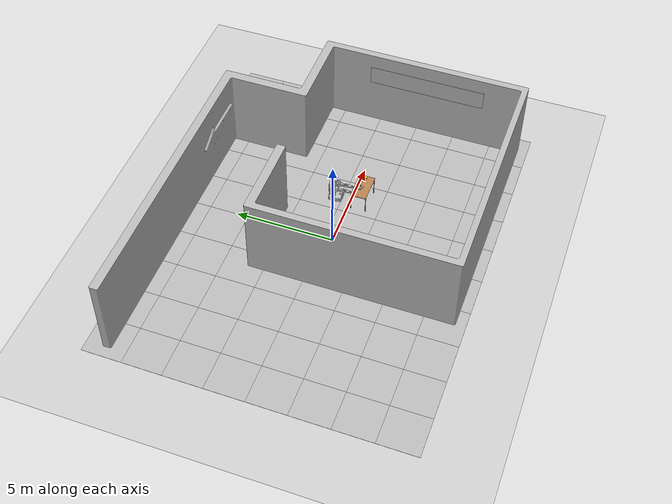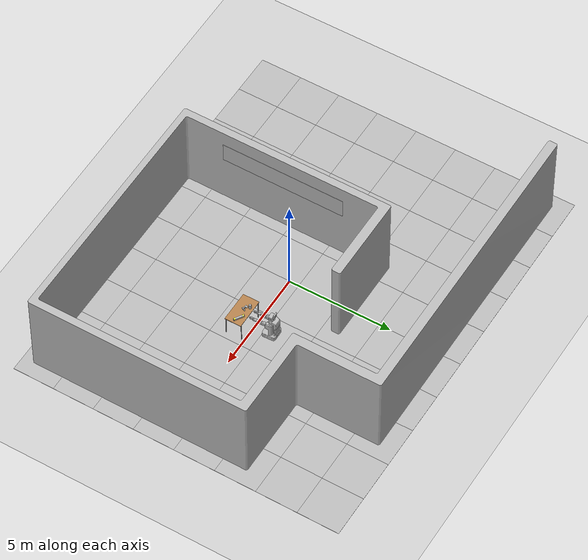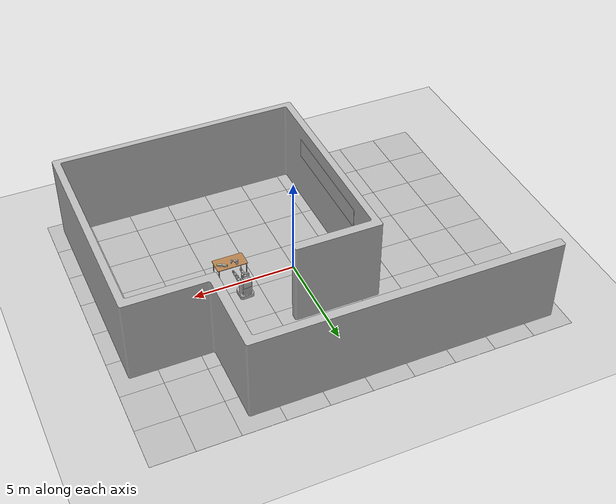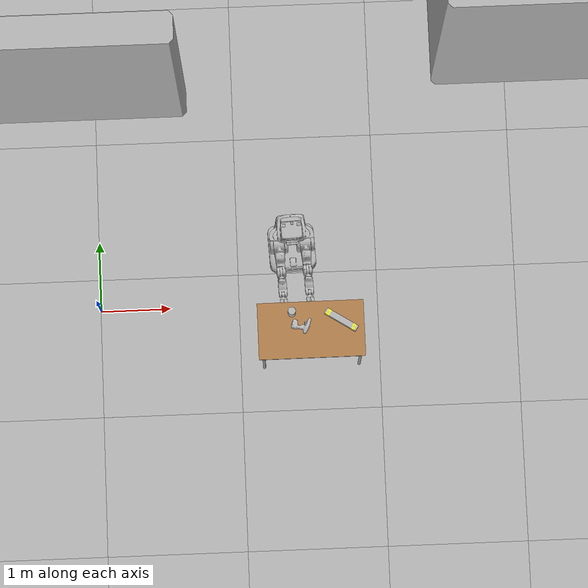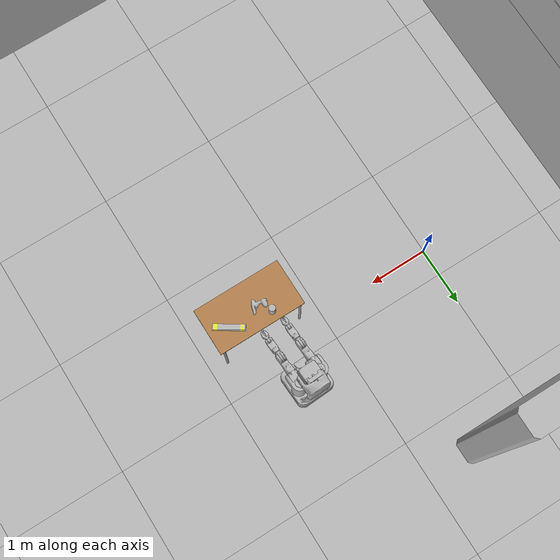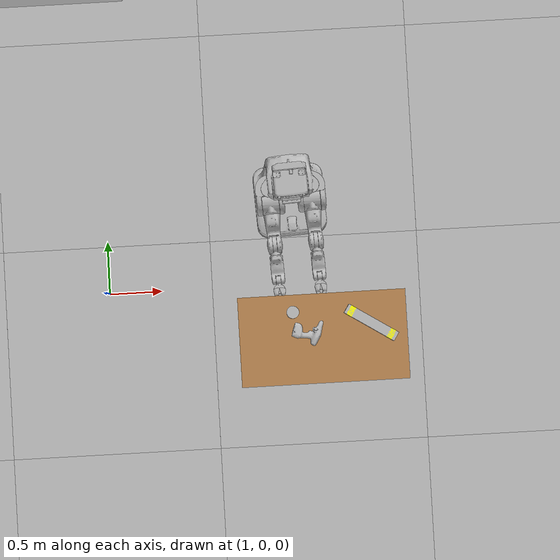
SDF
<sdf version="1.4">
 <world name="default">
  <light name="sun" type="directional">
   <pose>0 0 10 0 -0 0</pose>
   <diffuse>0.8 0.8 0.8 1</diffuse>
   <specular>0.2 0.2 0.2 1</specular>
   <attenuation>
    <range>1000</range>
    <constant>0.9</constant>
    <linear>0.01</linear>
    <quadratic>0.001</quadratic>
   </attenuation>
   <direction>-0.5 0.1 -0.9</direction>
  </light>
  <model name="ground_plane">
   <static>1</static>
   <link name="link">
    <collision name="collision">
     <geometry><plane><normal>0 0 1</normal><size>100 100</size></plane></geometry>
     <surface><friction><ode><mu>100</mu><mu2>50</mu2></ode></friction></surface>
    </collision>
    <visual name="visual">
     <cast_shadows>0</cast_shadows>
     <geometry><plane><normal>0 0 1</normal><size>100 100</size></plane></geometry>
     <material>
      <script><uri>file://media/materials/scripts/gazebo.material</uri><name>Gazebo/Grey</name></script>
     </material>
    </visual>
    <velocity_decay><linear>0</linear><angular>0</angular></velocity_decay>
   </link>
  </model>
  <physics type="ode">
   <max_step_size>0.001</max_step_size>
   <real_time_factor>1</real_time_factor>
   <real_time_update_rate>1000</real_time_update_rate>
   <gravity>0 0 -9.8</gravity>
  </physics>
  <scene><ambient>0.4 0.4 0.4 1</ambient><background>0.7 0.7 0.7 1</background><shadows>1</shadows></scene>
  <model name="pr2">
   <link name="base_footprint">
    <inertial>
     <pose>-0.0624209 0 0.201365 0 -0 0</pose>
     <mass>118.001</mass>
     <inertia>
      <ixx>6.13665</ixx>
      <ixy>-0.00971993</ixy>
      <ixz>1.455</ixz>
      <iyy>6.20983</iyy>
      <iyz>-0.00737958</iyz>
      <izz>3.75933</izz>
     </inertia>
    </inertial>
    <collision name="base_footprint_collision">
     <pose>0 0 0.071 0 -0 0</pose>
     <geometry><box><size>0.001 0.001 0.001</size></box></geometry>
    </collision>
    <collision name="base_footprint_collision_base_bellow_link">
     <pose>-0.29 0 0.851 0 -0 0</pose>
     <geometry><box><size>0.05 0.37 0.3</size></box></geometry>
    </collision>
    <collision name="base_footprint_collision_base_link">
     <pose>0 0 0.051 0 -0 0</pose>
     <geometry>
      <mesh><scale>1 1 1</scale><uri>/opt/ros/hydro/share/pr2_description/meshes/base_v0/base_L.stl</uri></mesh>
     </geometry>
    </collision>
    <visual name="base_footprint_visual"><geometry><box><size>0.01 0.01 0.01</size></box></geometry></visual>
    <visual name="base_footprint_visual_base_bellow_link">
     <pose>-0.29 0 0.851 0 -0 0</pose>
     <geometry><box><size>0.05 0.37 0.3</size></box></geometry>
     <material><script><name>PR2/Black</name><uri>__default__</uri></script></material>
    </visual>
    <visual name="base_footprint_visual_base_link">
     <pose>0 0 0.051 0 -0 0</pose>
     <geometry>
      <mesh><scale>1 1 1</scale><uri>/opt/ros/hydro/share/pr2_description/meshes/base_v0/base.dae</uri></mesh>
     </geometry>
    </visual>
    <velocity_decay><linear>0</linear><angular>0</angular></velocity_decay>
    <sensor name="base_contact_sensor" type="contact">
     <always_on>1</always_on>
     <update_rate>100</update_rate>
     <contact><collision>base_link_geom</collision><topic>__default_topic__</topic></contact>
     <plugin name="base_gazebo_ros_bumper_controller" filename="libgazebo_ros_bumper.so">
      <alwaysOn>true</alwaysOn>
      <updateRate>100.0</updateRate>
      <bumperTopicName>base_bumper</bumperTopicName>
      <frameName>world</frameName>
      <robotNamespace>/</robotNamespace>
     </plugin>
     <pose>0 0 0.051 0 -0 0</pose>
    </sensor>
    <velocity_decay><linear>0</linear><angular>0</angular></velocity_decay>
    <velocity_decay><linear>0</linear><angular>0</angular></velocity_decay>
    <sensor name="base_laser" type="ray">
     <always_on>1</always_on>
     <update_rate>20</update_rate>
     <visualize>0</visualize>
     <ray>
      <scan>
       <horizontal>
        <samples>640</samples>
        <resolution>1</resolution>
        <min_angle>-2.2689</min_angle>
        <max_angle>2.2689</max_angle>
       </horizontal>
      </scan>
      <range><min>0.08</min><max>10</max><resolution>0.01</resolution></range>
     </ray>
     <plugin name="gazebo_ros_base_laser_controller" filename="libgazebo_ros_laser.so">
      <gaussianNoise>0.005</gaussianNoise>
      <alwaysOn>true</alwaysOn>
      <updateRate>20</updateRate>
      <topicName>base_scan</topicName>
      <frameName>base_laser_link</frameName>
      <hokuyoMinIntensity>101</hokuyoMinIntensity>
      <robotNamespace>/</robotNamespace>
     </plugin>
     <pose>0.275 0 0.303 0 -0 0</pose>
    </sensor>
   </link>
   <link name="bl_caster_rotation_link">
    <pose>-0.2246 0.2246 0.0792 0 -0 0</pose>
    <inertial>
     <pose>0 0 0.07 0 -0 0</pose>
     <mass>3.47308</mass>
     <inertia>
      <ixx>0.0124118</ixx>
      <ixy>-0.000711734</ixy>
      <ixz>0.00050273</ixz>
      <iyy>0.0152182</iyy>
      <iyz>-4.27347e-06</iyz>
      <izz>0.011764</izz>
     </inertia>
    </inertial>
    <collision name="bl_caster_rotation_link_collision">
     <geometry>
      <mesh><scale>1 1 1</scale><uri>/opt/ros/hydro/share/pr2_description/meshes/base_v0/caster_L.stl</uri></mesh>
     </geometry>
    </collision>
    <visual name="bl_caster_rotation_link_visual">
     <geometry>
      <mesh><scale>1 1 1</scale><uri>/opt/ros/hydro/share/pr2_description/meshes/base_v0/caster.stl</uri></mesh>
     </geometry>
     <material><script><name>PR2/caster_texture</name><uri>__default__</uri></script></material>
    </visual>
    <velocity_decay><linear>0</linear><angular>0</angular></velocity_decay>
   </link>
   <joint name="bl_caster_rotation_joint" type="revolute">
    <child>bl_caster_rotation_link</child>
    <parent>base_footprint</parent>
    <axis>
     <xyz>0 0 1</xyz>
     <limit><lower>-1e+16</lower><upper>1e+16</upper></limit>
     <dynamics><damping>1</damping></dynamics>
    </axis>
   </joint>
   <link name="bl_caster_l_wheel_link">
    <pose>-0.2246 0.2736 0.0792 0 -0 0</pose>
    <inertial>
     <mass>0.44036</mass>
     <inertia>
      <ixx>0.0124118</ixx>
      <ixy>-0.000711734</ixy>
      <ixz>0.00050273</ixz>
      <iyy>0.0152182</iyy>
      <iyz>-4.27347e-06</iyz>
      <izz>0.011764</izz>
     </inertia>
    </inertial>
    <collision name="bl_caster_l_wheel_link_collision">
     <pose>0 0 0 1.5708 -0 0</pose>
     <geometry><cylinder><length>0.034</length><radius>0.074792</radius></cylinder></geometry>
     <surface>
      <contact><ode><kp>1e+06</kp><kd>1</kd><max_vel>100</max_vel><min_depth>0</min_depth></ode></contact>
      <friction><ode><mu>100</mu><mu2>100</mu2></ode></friction>
     </surface>
    </collision>
    <visual name="bl_caster_l_wheel_link_visual">
     <geometry>
      <mesh><scale>1 1 1</scale><uri>/opt/ros/hydro/share/pr2_description/meshes/base_v0/wheel.dae</uri></mesh>
     </geometry>
    </visual>
    <velocity_decay><linear>0</linear><angular>0</angular></velocity_decay>
   </link>
   <joint name="bl_caster_l_wheel_joint" type="revolute">
    <child>bl_caster_l_wheel_link</child>
    <parent>bl_caster_rotation_link</parent>
    <axis>
     <xyz>0 1 0</xyz>
     <limit><lower>-1e+16</lower><upper>1e+16</upper></limit>
     <dynamics><damping>1</damping></dynamics>
    </axis>
   </joint>
   <link name="bl_caster_r_wheel_link">
    <pose>-0.2246 0.1756 0.0792 0 -0 0</pose>
    <inertial>
     <mass>0.44036</mass>
     <inertia>
      <ixx>0.0124118</ixx>
      <ixy>-0.000711734</ixy>
      <ixz>0.00050273</ixz>
      <iyy>0.0152182</iyy>
      <iyz>-4.27347e-06</iyz>
      <izz>0.011764</izz>
     </inertia>
    </inertial>
    <collision name="bl_caster_r_wheel_link_collision">
     <pose>0 0 0 1.5708 -0 0</pose>
     <geometry><cylinder><length>0.034</length><radius>0.074792</radius></cylinder></geometry>
     <surface>
      <contact><ode><kp>1e+06</kp><kd>1</kd><max_vel>100</max_vel><min_depth>0</min_depth></ode></contact>
      <friction><ode><mu>100</mu><mu2>100</mu2></ode></friction>
     </surface>
    </collision>
    <visual name="bl_caster_r_wheel_link_visual">
     <geometry>
      <mesh><scale>1 1 1</scale><uri>/opt/ros/hydro/share/pr2_description/meshes/base_v0/wheel.dae</uri></mesh>
     </geometry>
    </visual>
    <velocity_decay><linear>0</linear><angular>0</angular></velocity_decay>
   </link>
   <joint name="bl_caster_r_wheel_joint" type="revolute">
    <child>bl_caster_r_wheel_link</child>
    <parent>bl_caster_rotation_link</parent>
    <axis>
     <xyz>0 1 0</xyz>
     <limit><lower>-1e+16</lower><upper>1e+16</upper></limit>
     <dynamics><damping>1</damping></dynamics>
    </axis>
   </joint>
   <link name="br_caster_rotation_link">
    <pose>-0.2246 -0.2246 0.0792 0 -0 0</pose>
    <inertial>
     <pose>0 0 0.07 0 -0 0</pose>
     <mass>3.47308</mass>
     <inertia>
      <ixx>0.0124118</ixx>
      <ixy>-0.000711734</ixy>
      <ixz>0.00050273</ixz>
      <iyy>0.0152182</iyy>
      <iyz>-4.27347e-06</iyz>
      <izz>0.011764</izz>
     </inertia>
    </inertial>
    <collision name="br_caster_rotation_link_collision">
     <geometry>
      <mesh><scale>1 1 1</scale><uri>/opt/ros/hydro/share/pr2_description/meshes/base_v0/caster_L.stl</uri></mesh>
     </geometry>
    </collision>
    <visual name="br_caster_rotation_link_visual">
     <geometry>
      <mesh><scale>1 1 1</scale><uri>/opt/ros/hydro/share/pr2_description/meshes/base_v0/caster.stl</uri></mesh>
     </geometry>
     <material><script><name>PR2/caster_texture</name><uri>__default__</uri></script></material>
    </visual>
    <velocity_decay><linear>0</linear><angular>0</angular></velocity_decay>
   </link>
   <joint name="br_caster_rotation_joint" type="revolute">
    <child>br_caster_rotation_link</child>
    <parent>base_footprint</parent>
    <axis>
     <xyz>0 0 1</xyz>
     <limit><lower>-1e+16</lower><upper>1e+16</upper></limit>
     <dynamics><damping>1</damping></dynamics>
    </axis>
   </joint>
   <link name="br_caster_l_wheel_link">
    <pose>-0.2246 -0.1756 0.0792 0 -0 0</pose>
    <inertial>
     <mass>0.44036</mass>
     <inertia>
      <ixx>0.0124118</ixx>
      <ixy>-0.000711734</ixy>
      <ixz>0.00050273</ixz>
      <iyy>0.0152182</iyy>
      <iyz>-4.27347e-06</iyz>
      <izz>0.011764</izz>
     </inertia>
    </inertial>
    <collision name="br_caster_l_wheel_link_collision">
     <pose>0 0 0 1.5708 -0 0</pose>
     <geometry><cylinder><length>0.034</length><radius>0.074792</radius></cylinder></geometry>
     <surface>
      <contact><ode><kp>1e+06</kp><kd>1</kd><max_vel>100</max_vel><min_depth>0</min_depth></ode></contact>
      <friction><ode><mu>100</mu><mu2>100</mu2></ode></friction>
     </surface>
    </collision>
    <visual name="br_caster_l_wheel_link_visual">
     <geometry>
      <mesh><scale>1 1 1</scale><uri>/opt/ros/hydro/share/pr2_description/meshes/base_v0/wheel.dae</uri></mesh>
     </geometry>
    </visual>
    <velocity_decay><linear>0</linear><angular>0</angular></velocity_decay>
   </link>
   <joint name="br_caster_l_wheel_joint" type="revolute">
    <child>br_caster_l_wheel_link</child>
    <parent>br_caster_rotation_link</parent>
    <axis>
     <xyz>0 1 0</xyz>
     <limit><lower>-1e+16</lower><upper>1e+16</upper></limit>
     <dynamics><damping>1</damping></dynamics>
    </axis>
   </joint>
   <link name="br_caster_r_wheel_link">
    <pose>-0.2246 -0.2736 0.0792 0 -0 0</pose>
    <inertial>
     <mass>0.44036</mass>
     <inertia>
      <ixx>0.0124118</ixx>
      <ixy>-0.000711734</ixy>
      <ixz>0.00050273</ixz>
      <iyy>0.0152182</iyy>
      <iyz>-4.27347e-06</iyz>
      <izz>0.011764</izz>
     </inertia>
    </inertial>
    <collision name="br_caster_r_wheel_link_collision">
     <pose>0 0 0 1.5708 -0 0</pose>
     <geometry><cylinder><length>0.034</length><radius>0.074792</radius></cylinder></geometry>
     <surface>
      <contact><ode><kp>1e+06</kp><kd>1</kd><max_vel>100</max_vel><min_depth>0</min_depth></ode></contact>
      <friction><ode><mu>100</mu><mu2>100</mu2></ode></friction>
     </surface>
    </collision>
    <visual name="br_caster_r_wheel_link_visual">
     <geometry>
      <mesh><scale>1 1 1</scale><uri>/opt/ros/hydro/share/pr2_description/meshes/base_v0/wheel.dae</uri></mesh>
     </geometry>
    </visual>
    <velocity_decay><linear>0</linear><angular>0</angular></velocity_decay>
   </link>
   <joint name="br_caster_r_wheel_joint" type="revolute">
    <child>br_caster_r_wheel_link</child>
    <parent>br_caster_rotation_link</parent>
    <axis>
     <xyz>0 1 0</xyz>
     <limit><lower>-1e+16</lower><upper>1e+16</upper></limit>
     <dynamics><damping>1</damping></dynamics>
    </axis>
   </joint>
   <link name="fl_caster_rotation_link">
    <pose>0.2246 0.2246 0.0792 0 -0 0</pose>
    <inertial>
     <pose>0 0 0.07 0 -0 0</pose>
     <mass>3.47308</mass>
     <inertia>
      <ixx>0.0124118</ixx>
      <ixy>-0.000711734</ixy>
      <ixz>0.00050273</ixz>
      <iyy>0.0152182</iyy>
      <iyz>-4.27347e-06</iyz>
      <izz>0.011764</izz>
     </inertia>
    </inertial>
    <collision name="fl_caster_rotation_link_collision">
     <geometry>
      <mesh><scale>1 1 1</scale><uri>/opt/ros/hydro/share/pr2_description/meshes/base_v0/caster_L.stl</uri></mesh>
     </geometry>
    </collision>
    <visual name="fl_caster_rotation_link_visual">
     <geometry>
      <mesh><scale>1 1 1</scale><uri>/opt/ros/hydro/share/pr2_description/meshes/base_v0/caster.stl</uri></mesh>
     </geometry>
     <material><script><name>PR2/caster_texture</name><uri>__default__</uri></script></material>
    </visual>
    <velocity_decay><linear>0</linear><angular>0</angular></velocity_decay>
   </link>
   <joint name="fl_caster_rotation_joint" type="revolute">
    <child>fl_caster_rotation_link</child>
    <parent>base_footprint</parent>
    <axis>
     <xyz>0 0 1</xyz>
     <limit><lower>-1e+16</lower><upper>1e+16</upper></limit>
     <dynamics><damping>1</damping></dynamics>
    </axis>
   </joint>
   <link name="fl_caster_l_wheel_link">
    <pose>0.2246 0.2736 0.0792 0 -0 0</pose>
    <inertial>
     <mass>0.44036</mass>
     <inertia>
      <ixx>0.0124118</ixx>
      <ixy>-0.000711734</ixy>
      <ixz>0.00050273</ixz>
      <iyy>0.0152182</iyy>
      <iyz>-4.27347e-06</iyz>
      <izz>0.011764</izz>
     </inertia>
    </inertial>
    <collision name="fl_caster_l_wheel_link_collision">
     <pose>0 0 0 1.5708 -0 0</pose>
     <geometry><cylinder><length>0.034</length><radius>0.074792</radius></cylinder></geometry>
     <surface>
      <contact><ode><kp>1e+06</kp><kd>1</kd><max_vel>100</max_vel><min_depth>0</min_depth></ode></contact>
      <friction><ode><mu>100</mu><mu2>100</mu2></ode></friction>
     </surface>
    </collision>
    <visual name="fl_caster_l_wheel_link_visual">
     <geometry>
      <mesh><scale>1 1 1</scale><uri>/opt/ros/hydro/share/pr2_description/meshes/base_v0/wheel.dae</uri></mesh>
     </geometry>
    </visual>
    <velocity_decay><linear>0</linear><angular>0</angular></velocity_decay>
   </link>
   <joint name="fl_caster_l_wheel_joint" type="revolute">
    <child>fl_caster_l_wheel_link</child>
    <parent>fl_caster_rotation_link</parent>
    <axis>
     <xyz>0 1 0</xyz>
     <limit><lower>-1e+16</lower><upper>1e+16</upper></limit>
     <dynamics><damping>1</damping></dynamics>
    </axis>
   </joint>
   <link name="fl_caster_r_wheel_link">
    <pose>0.2246 0.1756 0.0792 0 -0 0</pose>
    <inertial>
     <mass>0.44036</mass>
     <inertia>
      <ixx>0.0124118</ixx>
      <ixy>-0.000711734</ixy>
      <ixz>0.00050273</ixz>
      <iyy>0.0152182</iyy>
      <iyz>-4.27347e-06</iyz>
      <izz>0.011764</izz>
     </inertia>
    </inertial>
    <collision name="fl_caster_r_wheel_link_collision">
     <pose>0 0 0 1.5708 -0 0</pose>
     <geometry><cylinder><length>0.034</length><radius>0.074792</radius></cylinder></geometry>
     <surface>
      <contact><ode><kp>1e+06</kp><kd>1</kd><max_vel>100</max_vel><min_depth>0</min_depth></ode></contact>
      <friction><ode><mu>100</mu><mu2>100</mu2></ode></friction>
     </surface>
    </collision>
    <visual name="fl_caster_r_wheel_link_visual">
     <geometry>
      <mesh><scale>1 1 1</scale><uri>/opt/ros/hydro/share/pr2_description/meshes/base_v0/wheel.dae</uri></mesh>
     </geometry>
    </visual>
    <velocity_decay><linear>0</linear><angular>0</angular></velocity_decay>
   </link>
   <joint name="fl_caster_r_wheel_joint" type="revolute">
    <child>fl_caster_r_wheel_link</child>
    <parent>fl_caster_rotation_link</parent>
    <axis>
     <xyz>0 1 0</xyz>
     <limit><lower>-1e+16</lower><upper>1e+16</upper></limit>
     <dynamics><damping>1</damping></dynamics>
    </axis>
   </joint>
   <link name="fr_caster_rotation_link">
    <pose>0.2246 -0.2246 0.0792 0 -0 0</pose>
    <inertial>
     <pose>0 0 0.07 0 -0 0</pose>
     <mass>3.47308</mass>
     <inertia>
      <ixx>0.0124118</ixx>
      <ixy>-0.000711734</ixy>
      <ixz>0.00050273</ixz>
      <iyy>0.0152182</iyy>
      <iyz>-4.27347e-06</iyz>
      <izz>0.011764</izz>
     </inertia>
    </inertial>
    <collision name="fr_caster_rotation_link_collision">
     <geometry>
      <mesh><scale>1 1 1</scale><uri>/opt/ros/hydro/share/pr2_description/meshes/base_v0/caster_L.stl</uri></mesh>
     </geometry>
    </collision>
    <visual name="fr_caster_rotation_link_visual">
     <geometry>
      <mesh><scale>1 1 1</scale><uri>/opt/ros/hydro/share/pr2_description/meshes/base_v0/caster.stl</uri></mesh>
     </geometry>
     <material><script><name>PR2/caster_texture</name><uri>__default__</uri></script></material>
    </visual>
    <velocity_decay><linear>0</linear><angular>0</angular></velocity_decay>
   </link>
   <joint name="fr_caster_rotation_joint" type="revolute">
    <child>fr_caster_rotation_link</child>
    <parent>base_footprint</parent>
    <axis>
     <xyz>0 0 1</xyz>
     <limit><lower>-1e+16</lower><upper>1e+16</upper></limit>
     <dynamics><damping>1</damping></dynamics>
    </axis>
   </joint>
   <link name="fr_caster_l_wheel_link">
    <pose>0.2246 -0.1756 0.0792 0 -0 0</pose>
    <inertial>
     <mass>0.44036</mass>
     <inertia>
      <ixx>0.0124118</ixx>
      <ixy>-0.000711734</ixy>
      <ixz>0.00050273</ixz>
      <iyy>0.0152182</iyy>
      <iyz>-4.27347e-06</iyz>
      <izz>0.011764</izz>
     </inertia>
    </inertial>
    <collision name="fr_caster_l_wheel_link_collision">
     <pose>0 0 0 1.5708 -0 0</pose>
     <geometry><cylinder><length>0.034</length><radius>0.074792</radius></cylinder></geometry>
     <surface>
      <contact><ode><kp>1e+06</kp><kd>1</kd><max_vel>100</max_vel><min_depth>0</min_depth></ode></contact>
      <friction><ode><mu>100</mu><mu2>100</mu2></ode></friction>
     </surface>
    </collision>
    <visual name="fr_caster_l_wheel_link_visual">
     <geometry>
      <mesh><scale>1 1 1</scale><uri>/opt/ros/hydro/share/pr2_description/meshes/base_v0/wheel.dae</uri></mesh>
     </geometry>
    </visual>
    <velocity_decay><linear>0</linear><angular>0</angular></velocity_decay>
   </link>
   <joint name="fr_caster_l_wheel_joint" type="revolute">
    <child>fr_caster_l_wheel_link</child>
    <parent>fr_caster_rotation_link</parent>
    <axis>
     <xyz>0 1 0</xyz>
     <limit><lower>-1e+16</lower><upper>1e+16</upper></limit>
     <dynamics><damping>1</damping></dynamics>
    </axis>
   </joint>
   <link name="fr_caster_r_wheel_link">
    <pose>0.2246 -0.2736 0.0792 0 -0 0</pose>
    <inertial>
     <mass>0.44036</mass>
     <inertia>
      <ixx>0.0124118</ixx>
      <ixy>-0.000711734</ixy>
      <ixz>0.00050273</ixz>
      <iyy>0.0152182</iyy>
      <iyz>-4.27347e-06</iyz>
      <izz>0.011764</izz>
     </inertia>
    </inertial>
    <collision name="fr_caster_r_wheel_link_collision">
     <pose>0 0 0 1.5708 -0 0</pose>
     <geometry><cylinder><length>0.034</length><radius>0.074792</radius></cylinder></geometry>
     <surface>
      <contact><ode><kp>1e+06</kp><kd>1</kd><max_vel>100</max_vel><min_depth>0</min_depth></ode></contact>
      <friction><ode><mu>100</mu><mu2>100</mu2></ode></friction>
     </surface>
    </collision>
    <visual name="fr_caster_r_wheel_link_visual">
     <geometry>
      <mesh><scale>1 1 1</scale><uri>/opt/ros/hydro/share/pr2_description/meshes/base_v0/wheel.dae</uri></mesh>
     </geometry>
    </visual>
    <velocity_decay><linear>0</linear><angular>0</angular></velocity_decay>
   </link>
   <joint name="fr_caster_r_wheel_joint" type="revolute">
    <child>fr_caster_r_wheel_link</child>
    <parent>fr_caster_rotation_link</parent>
    <axis>
     <xyz>0 1 0</xyz>
     <limit><lower>-1e+16</lower><upper>1e+16</upper></limit>
     <dynamics><damping>1</damping></dynamics>
    </axis>
   </joint>
   <link name="torso_lift_link">
    <pose>-0.05 0 0.790675 0 -0 0</pose>
    <inertial>
     <pose>-0.0994987 -4.1071e-06 -0.0867639 0 -0 0</pose>
     <mass>36.449</mass>
     <inertia>
      <ixx>2.80235</ixx>
      <ixy>0.00429496</ixy>
      <ixz>-0.16614</ixz>
      <iyy>2.53349</iyy>
      <iyz>0.029702</iyz>
      <izz>0.538967</izz>
     </inertia>
    </inertial>
    <collision name="torso_lift_link_collision">
     <geometry>
      <mesh>
       <scale>1 1 1</scale>
       <uri>/opt/ros/hydro/share/pr2_description/meshes/torso_v0/torso_lift_L.stl</uri>
      </mesh>
     </geometry>
    </collision>
    <visual name="torso_lift_link_visual">
     <geometry>
      <mesh>
       <scale>1 1 1</scale>
       <uri>/opt/ros/hydro/share/pr2_description/meshes/torso_v0/torso_lift.dae</uri>
      </mesh>
     </geometry>
    </visual>
    <velocity_decay><linear>0</linear><angular>0</angular></velocity_decay>
    <sensor name="torso_lift_contact_sensor" type="contact">
     <contact><collision>torso_lift_link_geom</collision><topic>__default_topic__</topic></contact>
     <update_rate>100</update_rate>
     <plugin name="torso_lift_gazebo_ros_bumper_controller" filename="libgazebo_ros_bumper.so">
      <alwaysOn>true</alwaysOn>
      <updateRate>100.0</updateRate>
      <bumperTopicName>torso_lift_bumper</bumperTopicName>
      <frameName>world</frameName>
      <robotNamespace>/</robotNamespace>
     </plugin>
    </sensor>
   </link>
   <joint name="torso_lift_joint" type="prismatic">
    <child>torso_lift_link</child>
    <parent>base_footprint</parent>
    <axis>
     <xyz>0 0 1</xyz>
     <limit><lower>0</lower><upper>0.33</upper><effort>10000</effort><velocity>0.013</velocity></limit>
     <dynamics><damping>20000</damping></dynamics>
    </axis>
   </joint>
   <link name="head_pan_link">
    <pose>-0.06707 0 1.17213 0 -0 0</pose>
    <inertial>
     <pose>0.010907 0.031693 0.090507 0 -0 0</pose>
     <mass>6.339</mass>
     <inertia>
      <ixx>0.0324976</ixx>
      <ixy>0.000636041</ixy>
      <ixz>0.00258515</ixz>
      <iyy>0.0465456</iyy>
      <iyz>-0.00245343</iyz>
      <izz>0.0576527</izz>
     </inertia>
    </inertial>
    <collision name="head_pan_link_collision">
     <geometry>
      <mesh><scale>1 1 1</scale><uri>/opt/ros/hydro/share/pr2_description/meshes/head_v0/head_pan_L.stl</uri></mesh>
     </geometry>
    </collision>
    <visual name="head_pan_link_visual">
     <geometry>
      <mesh><scale>1 1 1</scale><uri>/opt/ros/hydro/share/pr2_description/meshes/head_v0/head_pan.dae</uri></mesh>
     </geometry>
    </visual>
    <velocity_decay><linear>0</linear><angular>0</angular></velocity_decay>
   </link>
   <joint name="head_pan_joint" type="revolute">
    <child>head_pan_link</child>
    <parent>torso_lift_link</parent>
    <axis>
     <xyz>0 0 1</xyz>
     <limit><lower>-3.007</lower><upper>3.007</upper><effort>2.645</effort><velocity>6</velocity></limit>
     <dynamics><damping>0.5</damping></dynamics>
    </axis>
   </joint>
   <link name="head_tilt_link">
    <pose>0.00093 0 1.17213 0 -0 0</pose>
    <inertial>
     <pose>-0.00515059 -0.0146346 0.0728191 0 -0 0</pose>
     <mass>5.319</mass>
     <inertia>
      <ixx>0.112053</ixx>
      <ixy>0.000788314</ixy>
      <ixz>0.00946294</ixz>
      <iyy>0.150319</iyy>
      <iyz>0.000755439</iyz>
      <izz>0.167392</izz>
     </inertia>
    </inertial>
    <collision name="head_tilt_link_collision">
     <geometry>
      <mesh>
       <scale>1 1 1</scale>
       <uri>/opt/ros/hydro/share/pr2_description/meshes/head_v0/head_tilt_L.stl</uri>
      </mesh>
     </geometry>
    </collision>
    <collision name="head_tilt_link_collision_head_mount_kinect_ir_link">
     <pose>-0.147067 0.0125 0.291953 0 -0 0</pose>
     <geometry><sphere><radius>0.0005</radius></sphere></geometry>
    </collision>
    <collision name="head_tilt_link_collision_head_mount_kinect_rgb_link">
     <pose>-0.147067 -0.0175 0.291953 0 -0 0</pose>
     <geometry><sphere><radius>0.0005</radius></sphere></geometry>
    </collision>
    <collision name="head_tilt_link_collision_head_mount_link">
     <pose>-0.1148 0 0.1555 0 -0 0</pose>
     <geometry><sphere><radius>0.0005</radius></sphere></geometry>
    </collision>
    <collision name="head_tilt_link_collision_head_mount_prosilica_link">
     <pose>-0.161257 0.0125 0.244421 0 -0 0</pose>
     <geometry><sphere><radius>0.0005</radius></sphere></geometry>
    </collision>
    <collision name="head_tilt_link_collision_head_plate_frame">
     <pose>0.0232 0 0.0645 0 -0 0</pose>
     <geometry><box><size>0.01 0.01 0.01</size></box></geometry>
    </collision>
    <visual name="head_tilt_link_visual">
     <geometry>
      <mesh><scale>1 1 1</scale><uri>/opt/ros/hydro/share/pr2_description/meshes/head_v0/head_tilt.dae</uri></mesh>
     </geometry>
    </visual>
    <visual name="head_tilt_link_visual_double_stereo_link">
     <pose>0.0132 0 0.0895 0 -0 0</pose>
     <geometry><box><size>0.02 0.12 0.05</size></box></geometry>
    </visual>
    <visual name="head_tilt_link_visual_head_mount_kinect_ir_link">
     <pose>-0.147067 0.0125 0.291953 0 -0 0</pose>
     <geometry><sphere><radius>0.0005</radius></sphere></geometry>
     <material><script><name>Gazebo/Red</name><uri>__default__</uri></script></material>
    </visual>
    <visual name="head_tilt_link_visual_head_mount_kinect_rgb_link">
     <pose>-0.147067 -0.0175 0.291953 0 -0 0</pose>
     <geometry><sphere><radius>0.0005</radius></sphere></geometry>
     <material><script><name>Gazebo/Red</name><uri>__default__</uri></script></material>
    </visual>
    <visual name="head_tilt_link_visual_head_mount_link">
     <pose>-0.1148 0 0.1555 0 -0 0</pose>
     <geometry>
      <mesh>
       <scale>0.001 0.001 0.001</scale>
       <uri>/opt/ros/hydro/share/pr2_description/meshes/sensors/kinect_prosilica_v0/115x100_swept_back--coarse.STL</uri>
      </mesh>
     </geometry>
    </visual>
    <visual name="head_tilt_link_visual_head_mount_prosilica_link">
     <pose>-0.161257 0.0125 0.244421 0 -0 0</pose>
     <geometry><sphere><radius>0.0005</radius></sphere></geometry>
     <material><script><name>Gazebo/Red</name><uri>__default__</uri></script></material>
    </visual>
    <visual name="head_tilt_link_visual_head_plate_frame">
     <pose>0.0232 0 0.0645 0 -0 0</pose>
     <geometry><box><size>0.01 0.01 0.01</size></box></geometry>
     <material><script><name>Gazebo/Grey</name><uri>__default__</uri></script></material>
    </visual>
    <visual name="head_tilt_link_visual_sensor_mount_link">
     <pose>0.0232 0 0.0645 0 -0 0</pose>
     <geometry><box><size>0.01 0.01 0.01</size></box></geometry>
    </visual>
    <velocity_decay><linear>0</linear><angular>0</angular></velocity_decay>
    <velocity_decay><linear>0</linear><angular>0</angular></velocity_decay>
    <sensor name="head_mount_ir_sensor" type="depth">
     <always_on>1</always_on>
     <update_rate>1</update_rate>
     <camera name="__default__">
      <horizontal_fov>0.994838</horizontal_fov>
      <image><format>L8</format><width>640</width><height>480</height></image>
      <clip><near>0.01</near><far>5</far></clip>
     </camera>
     <plugin name="head_mount_kinect_ir_link_controller" filename="libgazebo_ros_openni_kinect.so">
      <baseline>0.2</baseline>
      <alwaysOn>true</alwaysOn>
      <updateRate>1.0</updateRate>
      <cameraName>head_mount_kinect_ir</cameraName>
      <imageTopicName>/head_mount_kinect/depth/image_raw</imageTopicName>
      <cameraInfoTopicName>/head_mount_kinect/depth/camera_info</cameraInfoTopicName>
      <depthImageTopicName>/head_mount_kinect/depth/image_raw</depthImageTopicName>
      <depthImageCameraInfoTopicName>/head_mount_kinect/depth/camera_info</depthImageCameraInfoTopicName>
      <pointCloudTopicName>/head_mount_kinect/depth/points</pointCloudTopicName>
      <frameName>head_mount_kinect_ir_optical_frame</frameName>
      <pointCloudCutoff>0.5</pointCloudCutoff>
      <distortionK1>0.00000001</distortionK1>
      <distortionK2>0.00000001</distortionK2>
      <distortionK3>0.00000001</distortionK3>
      <distortionT1>0.00000001</distortionT1>
      <distortionT2>0.00000001</distortionT2>
      <CxPrime>0</CxPrime>
      <Cx>0</Cx>
      <Cy>0</Cy>
      <focalLength>0</focalLength>
      <hackBaseline>0</hackBaseline>
      <robotNamespace>/</robotNamespace>
     </plugin>
     <pose>-0.147067 0.0125 0.291953 0 -0 0</pose>
    </sensor>
    <velocity_decay><linear>0</linear><angular>0</angular></velocity_decay>
    <sensor name="head_mount_rgb_sensor" type="depth">
     <always_on>1</always_on>
     <update_rate>1</update_rate>
     <camera name="__default__">
      <horizontal_fov>0.994838</horizontal_fov>
      <image><format>R8G8B8</format><width>640</width><height>480</height></image>
      <clip><near>0.01</near><far>5</far></clip>
     </camera>
     <plugin name="head_mount_kinect_rgb_link_controller" filename="libgazebo_ros_openni_kinect.so">
      <alwaysOn>true</alwaysOn>
      <updateRate>1.0</updateRate>
      <cameraName>head_mount_kinect_rgb</cameraName>
      <imageTopicName>/head_mount_kinect/rgb/image_raw</imageTopicName>
      <cameraInfoTopicName>/head_mount_kinect/rgb/camera_info</cameraInfoTopicName>
      <depthImageTopicName>/head_mount_kinect/depth/image_raw</depthImageTopicName>
      <depthImageCameraInfoTopicName>/head_mount_kinect/depth/camera_info</depthImageCameraInfoTopicName>
      <pointCloudTopicName>/head_mount_kinect/depth_registered/points</pointCloudTopicName>
      <frameName>head_mount_kinect_rgb_optical_frame</frameName>
      <pointCloudCutoff>0.5</pointCloudCutoff>
      <distortionK1>0.00000001</distortionK1>
      <distortionK2>0.00000001</distortionK2>
      <distortionK3>0.00000001</distortionK3>
      <distortionT1>0.00000001</distortionT1>
      <distortionT2>0.00000001</distortionT2>
      <CxPrime>0</CxPrime>
      <Cx>0</Cx>
      <Cy>0</Cy>
      <focalLength>0</focalLength>
      <hackBaseline>0</hackBaseline>
      <robotNamespace>/</robotNamespace>
     </plugin>
     <pose>-0.147067 -0.0175 0.291953 0 -0 0</pose>
    </sensor>
    <velocity_decay><linear>0</linear><angular>0</angular></velocity_decay>
    <sensor name="head_mount_prosilica_link_sensor" type="camera">
     <always_on>1</always_on>
     <update_rate>1</update_rate>
     <camera name="__default__">
      <horizontal_fov>1.1205</horizontal_fov>
      <image><format>R8G8B8</format><width>320</width><height>240</height></image>
      <clip><near>0.1</near><far>100</far></clip>
     </camera>
     <plugin name="head_mount_prosilica_link_controller" filename="libgazebo_ros_prosilica.so">
      <alwaysOn>true</alwaysOn>
      <updateRate>1.0</updateRate>
      <cameraName>prosilica_camera_1mb</cameraName>
      <imageTopicName>image_raw</imageTopicName>
      <cameraInfoTopicName>camera_info</cameraInfoTopicName>
      <depthImageTopicName>depth/image_raw</depthImageTopicName>
      <depthImageCameraInfoTopicName>depth/camera_info</depthImageCameraInfoTopicName>
      <pollServiceName>request_image</pollServiceName>
      <pointCloudTopicName>points</pointCloudTopicName>
      <frameName>head_mount_prosilica_optical_frame</frameName>
      <pointCloudCutoff>0.4</pointCloudCutoff>
      <distortionK1>0.0</distortionK1>
      <distortionK2>0.0</distortionK2>
      <distortionK3>0.0</distortionK3>
      <distortionT1>0.0</distortionT1>
      <distortionT2>0.0</distortionT2>
      <CxPrime>0</CxPrime>
      <Cx>0</Cx>
      <Cy>0</Cy>
      <focalLength>0</focalLength>
      <hackBaseline>0</hackBaseline>
      <robotNamespace>/</robotNamespace>
     </plugin>
     <pose>-0.161257 0.0125 0.244421 0 -0 0</pose>
    </sensor>
    <sensor name="head_mount_prosilica_link_sim_pcd_sensor" type="depth">
     <always_on>1</always_on>
     <update_rate>1</update_rate>
     <camera name="__default__">
      <horizontal_fov>1.1205</horizontal_fov>
      <image><format>R8G8B8</format><width>320</width><height>240</height></image>
      <clip><near>0.1</near><far>100</far></clip>
     </camera>
     <plugin name="head_mount_prosilica_link_sim_pcd_controller" filename="libgazebo_ros_openni_kinect.so">
      <alwaysOn>true</alwaysOn>
      <updateRate>1.0</updateRate>
      <cameraName>prosilica_camera_1mb_sim_pcd</cameraName>
      <imageTopicName>image_raw</imageTopicName>
      <depthImageTopicName>depth/image_raw</depthImageTopicName>
      <depthImageCameraInfoTopicName>depth/camera_info</depthImageCameraInfoTopicName>
      <cameraInfoTopicName>camera_info</cameraInfoTopicName>
      <pointCloudTopicName>points</pointCloudTopicName>
      <frameName>head_mount_prosilica_optical_frame</frameName>
      <pointCloudCutoff>0.4</pointCloudCutoff>
      <distortionK1>0.00000001</distortionK1>
      <distortionK2>0.00000001</distortionK2>
      <distortionK3>0.00000001</distortionK3>
      <distortionT1>0.00000001</distortionT1>
      <distortionT2>0.00000001</distortionT2>
      <CxPrime>0</CxPrime>
      <Cx>0</Cx>
      <Cy>0</Cy>
      <focalLength>0</focalLength>
      <hackBaseline>0</hackBaseline>
      <robotNamespace>/</robotNamespace>
     </plugin>
     <pose>-0.161257 0.0125 0.244421 0 -0 0</pose>
    </sensor>
    <velocity_decay><linear>0</linear><angular>0</angular></velocity_decay>
    <projector name="projector_wg6802418_projector_wg6802418">
     <texture>stereo_projection_pattern_high_res_red.png</texture>
     <fov>0.959931</fov>
     <near_clip>0.1</near_clip>
     <far_clip>10</far_clip>
     <pose>0.0232 0.11 0.1191 3.14159 -1.57079 3.14159</pose>
    </projector>
    <velocity_decay><linear>0</linear><angular>0</angular></velocity_decay>
    <velocity_decay><linear>0</linear><angular>0</angular></velocity_decay>
    <sensor name="narrow_stereo_l_stereo_camera_sensor" type="camera">
     <always_on>1</always_on>
     <update_rate>25</update_rate>
     <camera name="__default__">
      <horizontal_fov>0.785398</horizontal_fov>
      <image><format>L8</format><width>640</width><height>480</height></image>
      <clip><near>0.1</near><far>100</far></clip>
     </camera>
     <plugin name="narrow_stereo_l_stereo_camera_controller" filename="libgazebo_ros_camera.so">
      <alwaysOn>true</alwaysOn>
      <updateRate>25.0</updateRate>
      <cameraName>narrow_stereo/left</cameraName>
      <imageTopicName>image_raw</imageTopicName>
      <cameraInfoTopicName>camera_info</cameraInfoTopicName>
      <frameName>narrow_stereo_optical_frame</frameName>
      <hackBaseline>0</hackBaseline>
      <CxPrime>320.5</CxPrime>
      <Cx>320.5</Cx>
      <Cy>240.5</Cy>
      <focalLength>772.548518</focalLength>
      <distortionK1>0.0</distortionK1>
      <distortionK2>0.0</distortionK2>
      <distortionK3>0.0</distortionK3>
      <distortionT1>0.0</distortionT1>
      <distortionT2>0.0</distortionT2>
      <robotNamespace>/</robotNamespace>
     </plugin>
     <pose>0.0682 0.06 0.1146 0 -0 0</pose>
    </sensor>
    <velocity_decay><linear>0</linear><angular>0</angular></velocity_decay>
    <sensor name="narrow_stereo_r_stereo_camera_sensor" type="camera">
     <always_on>1</always_on>
     <update_rate>25</update_rate>
     <camera name="__default__">
      <horizontal_fov>0.785398</horizontal_fov>
      <image><format>L8</format><width>640</width><height>480</height></image>
      <clip><near>0.1</near><far>100</far></clip>
     </camera>
     <plugin name="narrow_stereo_r_stereo_camera_controller" filename="libgazebo_ros_camera.so">
      <alwaysOn>true</alwaysOn>
      <updateRate>25.0</updateRate>
      <cameraName>narrow_stereo/right</cameraName>
      <imageTopicName>image_raw</imageTopicName>
      <cameraInfoTopicName>camera_info</cameraInfoTopicName>
      <frameName>narrow_stereo_optical_frame</frameName>
      <hackBaseline>0.09</hackBaseline>
      <CxPrime>320.5</CxPrime>
      <Cx>320.5</Cx>
      <Cy>240.5</Cy>
      <focalLength>772.548518</focalLength>
      <distortionK1>0.0</distortionK1>
      <distortionK2>0.0</distortionK2>
      <distortionK3>0.0</distortionK3>
      <distortionT1>0.0</distortionT1>
      <distortionT2>0.0</distortionT2>
      <robotNamespace>/</robotNamespace>
     </plugin>
     <pose>0.0682 -0.03 0.1146 0 -0 0</pose>
    </sensor>
    <velocity_decay><linear>0</linear><angular>0</angular></velocity_decay>
    <velocity_decay><linear>0</linear><angular>0</angular></velocity_decay>
    <velocity_decay><linear>0</linear><angular>0</angular></velocity_decay>
    <sensor name="wide_stereo_l_stereo_camera_sensor" type="camera">
     <always_on>1</always_on>
     <update_rate>25</update_rate>
     <camera name="__default__">
      <horizontal_fov>1.5708</horizontal_fov>
      <image><format>BAYER_BGGR8</format><width>640</width><height>480</height></image>
      <clip><near>0.1</near><far>100</far></clip>
     </camera>
     <plugin name="wide_stereo_l_stereo_camera_controller" filename="libgazebo_ros_camera.so">
      <alwaysOn>true</alwaysOn>
      <updateRate>25.0</updateRate>
      <cameraName>wide_stereo/left</cameraName>
      <imageTopicName>image_raw</imageTopicName>
      <cameraInfoTopicName>camera_info</cameraInfoTopicName>
      <frameName>wide_stereo_optical_frame</frameName>
      <hackBaseline>0</hackBaseline>
      <CxPrime>320.5</CxPrime>
      <Cx>320.5</Cx>
      <Cy>240.5</Cy>
      <focalLength>320.000105</focalLength>
      <distortionK1>0.0</distortionK1>
      <distortionK2>0.0</distortionK2>
      <distortionK3>0.0</distortionK3>
      <distortionT1>0.0</distortionT1>
      <distortionT2>0.0</distortionT2>
      <robotNamespace>/</robotNamespace>
     </plugin>
     <pose>0.0682 0.03 0.1146 0 -0 0</pose>
    </sensor>
    <velocity_decay><linear>0</linear><angular>0</angular></velocity_decay>
    <sensor name="wide_stereo_r_stereo_camera_sensor" type="camera">
     <always_on>1</always_on>
     <update_rate>25</update_rate>
     <camera name="__default__">
      <horizontal_fov>1.5708</horizontal_fov>
      <image><format>BAYER_BGGR8</format><width>640</width><height>480</height></image>
      <clip><near>0.1</near><far>100</far></clip>
     </camera>
     <plugin name="wide_stereo_r_stereo_camera_controller" filename="libgazebo_ros_camera.so">
      <alwaysOn>true</alwaysOn>
      <updateRate>25.0</updateRate>
      <cameraName>wide_stereo/right</cameraName>
      <imageTopicName>image_raw</imageTopicName>
      <cameraInfoTopicName>camera_info</cameraInfoTopicName>
      <frameName>wide_stereo_optical_frame</frameName>
      <hackBaseline>0.09</hackBaseline>
      <CxPrime>320.5</CxPrime>
      <Cx>320.5</Cx>
      <Cy>240.5</Cy>
      <focalLength>320.000105</focalLength>
      <distortionK1>0.0</distortionK1>
      <distortionK2>0.0</distortionK2>
      <distortionK3>0.0</distortionK3>
      <distortionT1>0.0</distortionT1>
      <distortionT2>0.0</distortionT2>
      <robotNamespace>/</robotNamespace>
     </plugin>
     <pose>0.0682 -0.06 0.1146 0 -0 0</pose>
    </sensor>
    <velocity_decay><linear>0</linear><angular>0</angular></velocity_decay>
    <velocity_decay><linear>0</linear><angular>0</angular></velocity_decay>
    <sensor name="high_def_sensor" type="camera">
     <always_on>1</always_on>
     <update_rate>20</update_rate>
     <camera name="__default__">
      <horizontal_fov>0.785398</horizontal_fov>
      <image><format>R8G8B8</format><width>2448</width><height>2050</height></image>
      <clip><near>0.1</near><far>100</far></clip>
     </camera>
     <plugin name="high_def_controller" filename="libgazebo_ros_prosilica.so">
      <updateRate>20.0</updateRate>
      <cameraName>prosilica</cameraName>
      <imageTopicName>image_raw</imageTopicName>
      <cameraInfoTopicName>camera_info</cameraInfoTopicName>
      <pollServiceName>request_image</pollServiceName>
      <frameName>high_def_optical_frame</frameName>
      <CxPrime>1224.5</CxPrime>
      <Cx>1224.5</Cx>
      <Cy>1025.5</Cy>
      <focalLength>2954.998083</focalLength>
      <distortionK1>0.0</distortionK1>
      <distortionK2>0.0</distortionK2>
      <distortionK3>0.0</distortionK3>
      <distortionT1>0.0</distortionT1>
      <distortionT2>0.0</distortionT2>
      <robotNamespace>/</robotNamespace>
     </plugin>
     <pose>0.069657 -0.11 0.1191 0 -0 0</pose>
    </sensor>
   </link>
   <joint name="head_tilt_joint" type="revolute">
    <child>head_tilt_link</child>
    <parent>head_pan_link</parent>
    <axis>
     <xyz>0 1 0</xyz>
     <limit><lower>-0.471238</lower><upper>1.39626</upper><effort>18</effort><velocity>5</velocity></limit>
     <dynamics><damping>10</damping></dynamics>
    </axis>
   </joint>
   <link name="l_shoulder_pan_link">
    <pose>-0.05 0.188 0.790675 0 -0 0</pose>
    <inertial>
     <pose>-0.001201 0.024513 -0.098231 0 -0 0</pose>
     <mass>25.7993</mass>
     <inertia>
      <ixx>0.866179</ixx>
      <ixy>-0.0608651</ixy>
      <ixz>-0.121181</ixz>
      <iyy>0.874217</iyy>
      <iyz>-0.0588661</iyz>
      <izz>0.273538</izz>
     </inertia>
    </inertial>
    <collision name="l_shoulder_pan_link_collision">
     <geometry>
      <mesh>
       <scale>1 1 1</scale>
       <uri>/opt/ros/hydro/share/pr2_description/meshes/shoulder_v0/shoulder_pan.stl</uri>
      </mesh>
     </geometry>
    </collision>
    <visual name="l_shoulder_pan_link_visual">
     <geometry>
      <mesh>
       <scale>1 1 1</scale>
       <uri>/opt/ros/hydro/share/pr2_description/meshes/shoulder_v0/shoulder_pan.dae</uri>
      </mesh>
     </geometry>
    </visual>
    <gravity>0</gravity>
    <velocity_decay><linear>0</linear><angular>0</angular></velocity_decay>
   </link>
   <joint name="l_shoulder_pan_joint" type="revolute">
    <child>l_shoulder_pan_link</child>
    <parent>torso_lift_link</parent>
    <axis>
     <xyz>0 0 1</xyz>
     <limit><lower>-0.714602</lower><upper>2.2854</upper><effort>30</effort><velocity>2.088</velocity></limit>
     <dynamics><damping>10</damping></dynamics>
    </axis>
    <physics><ode><limit><cfm>0</cfm><erp>0.2</erp></limit></ode></physics>
   </joint>
   <link name="l_shoulder_lift_link">
    <pose>0.05 0.188 0.790675 0 -0 0</pose>
    <inertial>
     <pose>0.02195 -0.02664 -0.03127 0 -0 0</pose>
     <mass>2.74988</mass>
     <inertia>
      <ixx>0.0210558</ixx>
      <ixy>0.00496704</ixy>
      <ixz>-0.00194809</ixz>
      <iyy>0.0212722</iyy>
      <iyz>0.00110425</iyz>
      <izz>0.0197575</izz>
     </inertia>
    </inertial>
    <collision name="l_shoulder_lift_link_collision">
     <geometry>
      <mesh>
       <scale>1 1 1</scale>
       <uri>/opt/ros/hydro/share/pr2_description/meshes/shoulder_v0/shoulder_lift.stl</uri>
      </mesh>
     </geometry>
    </collision>
    <visual name="l_shoulder_lift_link_visual">
     <geometry>
      <mesh>
       <scale>1 1 1</scale>
       <uri>/opt/ros/hydro/share/pr2_description/meshes/shoulder_v0/shoulder_lift.dae</uri>
      </mesh>
     </geometry>
    </visual>
    <gravity>0</gravity>
    <velocity_decay><linear>0</linear><angular>0</angular></velocity_decay>
   </link>
   <joint name="l_shoulder_lift_joint" type="revolute">
    <child>l_shoulder_lift_link</child>
    <parent>l_shoulder_pan_link</parent>
    <axis>
     <xyz>0 1 0</xyz>
     <limit><lower>-0.5236</lower><upper>1.3963</upper><effort>30</effort><velocity>2.082</velocity></limit>
     <dynamics><damping>10</damping></dynamics>
    </axis>
    <physics><ode><limit><cfm>0</cfm><erp>0.2</erp></limit></ode></physics>
   </joint>
   <link name="l_upper_arm_roll_link">
    <pose>0.05 0.188 0.790675 0 -0 0</pose>
    <inertial>
     <pose>0.210551 0.016309 -0.000560683 0 -0 0</pose>
     <mass>6.11769</mass>
     <inertia>
      <ixx>0.0253331</ixx>
      <ixy>-0.00374234</ixy>
      <ixz>0.000619656</ixz>
      <iyy>0.0892438</iyy>
      <iyz>-0.000198608</iyz>
      <izz>0.0905498</izz>
     </inertia>
    </inertial>
    <collision name="l_upper_arm_roll_link_collision">
     <geometry>
      <mesh>
       <scale>1 1 1</scale>
       <uri>/opt/ros/hydro/share/pr2_description/meshes/shoulder_v0/upper_arm_roll_L.stl</uri>
      </mesh>
     </geometry>
    </collision>
    <collision name="l_upper_arm_roll_link_collision_l_upper_arm_link">
     <geometry>
      <mesh>
       <scale>1 1 1</scale>
       <uri>/opt/ros/hydro/share/pr2_description/meshes/upper_arm_v0/upper_arm.stl</uri>
      </mesh>
     </geometry>
    </collision>
    <visual name="l_upper_arm_roll_link_visual">
     <geometry>
      <mesh>
       <scale>1 1 1</scale>
       <uri>/opt/ros/hydro/share/pr2_description/meshes/shoulder_v0/upper_arm_roll.stl</uri>
      </mesh>
     </geometry>
     <material><script><name>PR2/RollLinks</name><uri>__default__</uri></script></material>
    </visual>
    <visual name="l_upper_arm_roll_link_visual_l_upper_arm_link">
     <geometry>
      <mesh>
       <scale>1 1 1</scale>
       <uri>/opt/ros/hydro/share/pr2_description/meshes/upper_arm_v0/upper_arm.dae</uri>
      </mesh>
     </geometry>
    </visual>
    <velocity_decay><linear>0</linear><angular>0</angular></velocity_decay>
    <gravity>0</gravity>
    <velocity_decay><linear>0</linear><angular>0</angular></velocity_decay>
   </link>
   <joint name="l_upper_arm_roll_joint" type="revolute">
    <child>l_upper_arm_roll_link</child>
    <parent>l_shoulder_lift_link</parent>
    <axis>
     <xyz>1 0 0</xyz>
     <limit><lower>-0.8</lower><upper>3.9</upper><effort>30</effort><velocity>3.27</velocity></limit>
     <dynamics><damping>0.1</damping></dynamics>
    </axis>
    <physics><ode><fudge_factor>0.5</fudge_factor><limit><cfm>0</cfm><erp>0.2</erp></limit></ode></physics>
   </joint>
   <link name="l_elbow_flex_link">
    <pose>0.45 0.188 0.790675 0 -0 0</pose>
    <inertial>
     <pose>0.01014 0.00032 -0.01211 0 -0 0</pose>
     <mass>1.90327</mass>
     <inertia>
      <ixx>0.00346542</ixx>
      <ixy>4.06683e-05</ixy>
      <ixz>0.000431716</ixz>
      <iyy>0.00441606</iyy>
      <iyz>-3.96891e-05</iyz>
      <izz>0.00359157</izz>
     </inertia>
    </inertial>
    <collision name="l_elbow_flex_link_collision">
     <geometry>
      <mesh>
       <scale>1 1 1</scale>
       <uri>/opt/ros/hydro/share/pr2_description/meshes/upper_arm_v0/elbow_flex.stl</uri>
      </mesh>
     </geometry>
    </collision>
    <visual name="l_elbow_flex_link_visual">
     <geometry>
      <mesh>
       <scale>1 1 1</scale>
       <uri>/opt/ros/hydro/share/pr2_description/meshes/upper_arm_v0/elbow_flex.dae</uri>
      </mesh>
     </geometry>
    </visual>
    <gravity>0</gravity>
    <velocity_decay><linear>0</linear><angular>0</angular></velocity_decay>
   </link>
   <joint name="l_elbow_flex_joint" type="revolute">
    <child>l_elbow_flex_link</child>
    <parent>l_upper_arm_roll_link</parent>
    <axis>
     <xyz>0 1 0</xyz>
     <limit><lower>-2.3213</lower><upper>0</upper><effort>30</effort><velocity>3.3</velocity></limit>
     <dynamics><damping>1</damping></dynamics>
    </axis>
    <physics><ode><limit><cfm>0</cfm><erp>0.2</erp></limit></ode></physics>
   </joint>
   <link name="l_forearm_roll_link">
    <pose>0.45 0.188 0.790675 0 -0 0</pose>
    <inertial>
     <pose>0.180727 -0.000163048 -0.00858343 0 -0 0</pose>
     <mass>2.68968</mass>
     <inertia>
      <ixx>0.0146843</ixx>
      <ixy>5.53089e-05</ixy>
      <ixz>0.000904462</ixz>
      <iyy>0.0295334</iyy>
      <iyz>-1.3343e-05</iyz>
      <izz>0.0310133</izz>
     </inertia>
    </inertial>
    <collision name="l_forearm_roll_link_collision">
     <geometry>
      <mesh>
       <scale>1 1 1</scale>
       <uri>/opt/ros/hydro/share/pr2_description/meshes/upper_arm_v0/forearm_roll_L.stl</uri>
      </mesh>
     </geometry>
    </collision>
    <collision name="l_forearm_roll_link_collision_l_forearm_link">
     <geometry>
      <mesh><scale>1 1 1</scale><uri>/opt/ros/hydro/share/pr2_description/meshes/forearm_v0/forearm.stl</uri></mesh>
     </geometry>
    </collision>
    <visual name="l_forearm_roll_link_visual">
     <geometry>
      <mesh>
       <scale>1 1 1</scale>
       <uri>/opt/ros/hydro/share/pr2_description/meshes/upper_arm_v0/forearm_roll.stl</uri>
      </mesh>
     </geometry>
     <material><script><name>PR2/RollLinks</name><uri>__default__</uri></script></material>
    </visual>
    <visual name="l_forearm_roll_link_visual_l_forearm_link">
     <geometry>
      <mesh><scale>1 1 1</scale><uri>/opt/ros/hydro/share/pr2_description/meshes/forearm_v0/forearm.dae</uri></mesh>
     </geometry>
    </visual>
    <velocity_decay><linear>0</linear><angular>0</angular></velocity_decay>
    <velocity_decay><linear>0</linear><angular>0</angular></velocity_decay>
    <sensor name="l_forearm_cam_sensor" type="camera">
     <always_on>1</always_on>
     <update_rate>25</update_rate>
     <camera name="__default__">
      <horizontal_fov>1.5708</horizontal_fov>
      <image><format>R8G8B8</format><width>640</width><height>480</height></image>
      <clip><near>0.1</near><far>100</far></clip>
     </camera>
     <plugin name="l_forearm_cam_controller" filename="libgazebo_ros_camera.so">
      <alwaysOn>true</alwaysOn>
      <updateRate>25.0</updateRate>
      <cameraName>l_forearm_cam</cameraName>
      <imageTopicName>image_raw</imageTopicName>
      <cameraInfoTopicName>camera_info</cameraInfoTopicName>
      <frameName>l_forearm_cam_optical_frame</frameName>
      <hackBaseline>0</hackBaseline>
      <CxPrime>320.5</CxPrime>
      <Cx>320.5</Cx>
      <Cy>240.5</Cy>
      <focalLength>320.000105</focalLength>
      <distortionK1>0.0</distortionK1>
      <distortionK2>0.0</distortionK2>
      <distortionK3>0.0</distortionK3>
      <distortionT1>0.0</distortionT1>
      <distortionT2>0.0</distortionT2>
      <robotNamespace>/</robotNamespace>
     </plugin>
     <pose>0.135 0 0.044 -1.5708 -0.562869 1.96911e-16</pose>
    </sensor>
    <gravity>0</gravity>
    <velocity_decay><linear>0</linear><angular>0</angular></velocity_decay>
   </link>
   <joint name="l_forearm_roll_joint" type="revolute">
    <child>l_forearm_roll_link</child>
    <parent>l_elbow_flex_link</parent>
    <axis>
     <xyz>1 0 0</xyz>
     <limit><lower>-1e+16</lower><upper>1e+16</upper></limit>
     <dynamics><damping>0.1</damping></dynamics>
    </axis>
    <physics><ode><fudge_factor>0.5</fudge_factor><limit><cfm>0</cfm><erp>0.2</erp></limit></ode></physics>
   </joint>
   <link name="l_wrist_flex_link">
    <pose>0.771 0.188 0.790675 0 -0 0</pose>
    <inertial>
     <pose>-0.00157 0 -0.00075 0 -0 0</pose>
     <mass>0.61402</mass>
     <inertia>
      <ixx>0.000651657</ixx>
      <ixy>2.8864e-07</ixy>
      <ixz>3.03477e-06</ixz>
      <iyy>0.000198244</iyy>
      <iyz>-2.2645e-07</iyz>
      <izz>0.000644505</izz>
     </inertia>
    </inertial>
    <collision name="l_wrist_flex_link_collision">
     <geometry>
      <mesh>
       <scale>1 1 1</scale>
       <uri>/opt/ros/hydro/share/pr2_description/meshes/forearm_v0/wrist_flex.stl</uri>
      </mesh>
     </geometry>
    </collision>
    <visual name="l_wrist_flex_link_visual">
     <geometry>
      <mesh>
       <scale>1 1 1</scale>
       <uri>/opt/ros/hydro/share/pr2_description/meshes/forearm_v0/wrist_flex.dae</uri>
      </mesh>
     </geometry>
    </visual>
    <gravity>0</gravity>
    <velocity_decay><linear>0</linear><angular>0</angular></velocity_decay>
   </link>
   <joint name="l_wrist_flex_joint" type="revolute">
    <child>l_wrist_flex_link</child>
    <parent>l_forearm_roll_link</parent>
    <axis>
     <xyz>0 1 0</xyz>
     <limit><lower>-2.18</lower><upper>0</upper><effort>10</effort><velocity>3.078</velocity></limit>
     <dynamics><damping>0.1</damping></dynamics>
    </axis>
    <physics><ode><limit><cfm>0</cfm><erp>0.2</erp></limit></ode></physics>
   </joint>
   <link name="l_wrist_roll_link">
    <pose>0.771 0.188 0.790675 0 -0 0</pose>
    <inertial>
     <pose>0.0564084 0.000451403 -0.00101353 0 -0 0</pose>
     <mass>0.68107</mass>
     <inertia>
      <ixx>0.0113524</ixx>
      <ixy>-1.88243e-05</ixy>
      <ixz>5.86222e-06</ixz>
      <iyy>0.0120549</iyy>
      <iyz>-5.41286e-07</iyz>
      <izz>0.012243</izz>
     </inertia>
    </inertial>
    <collision name="l_wrist_roll_link_collision">
     <geometry>
      <mesh>
       <scale>1 1 1</scale>
       <uri>/opt/ros/hydro/share/pr2_description/meshes/forearm_v0/wrist_roll_L.stl</uri>
      </mesh>
     </geometry>
    </collision>
    <collision name="l_wrist_roll_link_collision_l_gripper_motor_accelerometer_link">
     <geometry><box><size>0.001 0.001 0.001</size></box></geometry>
    </collision>
    <collision name="l_wrist_roll_link_collision_l_gripper_palm_link">
     <geometry>
      <mesh>
       <scale>1 1 1</scale>
       <uri>/opt/ros/hydro/share/pr2_description/meshes/gripper_v0/gripper_palm.stl</uri>
      </mesh>
     </geometry>
    </collision>
    <visual name="l_wrist_roll_link_visual">
     <geometry>
      <mesh>
       <scale>1 1 1</scale>
       <uri>/opt/ros/hydro/share/pr2_description/meshes/forearm_v0/wrist_roll.stl</uri>
      </mesh>
     </geometry>
     <material><script><name>PR2/RollLinks</name><uri>__default__</uri></script></material>
    </visual>
    <visual name="l_wrist_roll_link_visual_l_gripper_motor_accelerometer_link">
     <geometry><box><size>0.001 0.001 0.001</size></box></geometry>
    </visual>
    <visual name="l_wrist_roll_link_visual_l_gripper_palm_link">
     <geometry>
      <mesh>
       <scale>1 1 1</scale>
       <uri>/opt/ros/hydro/share/pr2_description/meshes/gripper_v0/gripper_palm.dae</uri>
      </mesh>
     </geometry>
    </visual>
    <velocity_decay><linear>0</linear><angular>0</angular></velocity_decay>
    <gravity>0</gravity>
    <velocity_decay><linear>0</linear><angular>0</angular></velocity_decay>
   </link>
   <joint name="l_wrist_roll_joint" type="revolute">
    <child>l_wrist_roll_link</child>
    <parent>l_wrist_flex_link</parent>
    <axis>
     <xyz>1 0 0</xyz>
     <limit><lower>-1e+16</lower><upper>1e+16</upper></limit>
     <dynamics><damping>0.1</damping></dynamics>
    </axis>
    <physics><ode><fudge_factor>0.5</fudge_factor><limit><cfm>0</cfm><erp>0.2</erp></limit></ode></physics>
   </joint>
   <link name="l_gripper_l_finger_link">
    <pose>0.84791 0.198 0.790675 0 -0 0</pose>
    <inertial>
     <pose>0.03598 0.0173 -0.00164 0 -0 0</pose>
     <mass>0.17126</mass>
     <inertia>
      <ixx>7.7562e-05</ixx>
      <ixy>1.49095e-06</ixy>
      <ixz>-9.83385e-06</ixz>
      <iyy>0.000197083</iyy>
      <iyz>-3.06125e-06</iyz>
      <izz>0.000181054</izz>
     </inertia>
    </inertial>
    <collision name="l_gripper_l_finger_link_collision">
     <geometry>
      <mesh>
       <scale>1 1 1</scale>
       <uri>/opt/ros/hydro/share/pr2_description/meshes/gripper_v0/l_finger.stl</uri>
      </mesh>
     </geometry>
     <surface>
      <contact><ode><kp>1e+06</kp><kd>1</kd></ode></contact>
      <friction><ode><mu>500</mu><mu2>500</mu2></ode></friction>
     </surface>
    </collision>
    <visual name="l_gripper_l_finger_link_visual">
     <geometry>
      <mesh>
       <scale>1 1 1</scale>
       <uri>/opt/ros/hydro/share/pr2_description/meshes/gripper_v0/l_finger.dae</uri>
      </mesh>
     </geometry>
    </visual>
    <gravity>0</gravity>
    <velocity_decay><linear>0</linear><angular>0</angular></velocity_decay>
   </link>
   <joint name="l_gripper_l_finger_joint" type="revolute">
    <child>l_gripper_l_finger_link</child>
    <parent>l_wrist_roll_link</parent>
    <axis>
     <xyz>0 0 1</xyz>
     <limit><lower>0</lower><upper>0.548</upper><effort>1000</effort><velocity>0.5</velocity></limit>
     <dynamics><damping>0.02</damping></dynamics>
    </axis>
    <physics>
     <provide_feedback>1</provide_feedback>
     <ode>
      <provide_feedback>1</provide_feedback>
      <fudge_factor>1</fudge_factor>
      <limit><cfm>0</cfm><erp>0.2</erp></limit>
     </ode>
    </physics>
   </joint>
   <link name="l_gripper_l_finger_tip_link">
    <pose>0.93928 0.20295 0.790675 0 -0 0</pose>
    <inertial>
     <pose>0.00423 0.00284 0 0 -0 0</pose>
     <mass>0.04419</mass>
     <inertia>
      <ixx>8.37047e-06</ixx>
      <ixy>5.83632e-06</ixy>
      <ixz>0</ixz>
      <iyy>9.87067e-06</iyy>
      <iyz>0</iyz>
      <izz>1.54177e-05</izz>
     </inertia>
    </inertial>
    <collision name="l_gripper_l_finger_tip_link_collision">
     <geometry>
      <mesh>
       <scale>1 1 1</scale>
       <uri>/opt/ros/hydro/share/pr2_description/meshes/gripper_v0/l_finger_tip.stl</uri>
      </mesh>
     </geometry>
     <surface>
      <contact><ode><kp>1e+07</kp><kd>1</kd></ode></contact>
      <friction><ode><mu>500</mu><mu2>500</mu2></ode></friction>
     </surface>
    </collision>
    <visual name="l_gripper_l_finger_tip_link_visual">
     <geometry>
      <mesh>
       <scale>1 1 1</scale>
       <uri>/opt/ros/hydro/share/pr2_description/meshes/gripper_v0/l_finger_tip.dae</uri>
      </mesh>
     </geometry>
    </visual>
    <gravity>0</gravity>
    <velocity_decay><linear>0</linear><angular>0</angular></velocity_decay>
    <sensor name="l_gripper_l_finger_tip_contact_sensor" type="contact">
     <update_rate>100</update_rate>
     <contact><collision>l_gripper_l_finger_tip_link_geom</collision><topic>__default_topic__</topic></contact>
     <plugin name="l_gripper_l_finger_tip_gazebo_ros_bumper_controller" filename="libgazebo_ros_bumper.so">
      <alwaysOn>true</alwaysOn>
      <frameName>l_gripper_l_finger_tip_link</frameName>
      <updateRate>100.0</updateRate>
      <bumperTopicName>l_gripper_l_finger_tip_bumper</bumperTopicName>
      <robotNamespace>/</robotNamespace>
     </plugin>
    </sensor>
   </link>
   <joint name="l_gripper_l_finger_tip_joint" type="revolute">
    <child>l_gripper_l_finger_tip_link</child>
    <parent>l_gripper_l_finger_link</parent>
    <axis>
     <xyz>0 0 -1</xyz>
     <limit><lower>0</lower><upper>0.548</upper><effort>1000</effort><velocity>0.5</velocity></limit>
     <dynamics><damping>0.001</damping></dynamics>
    </axis>
    <physics>
     <provide_feedback>1</provide_feedback>
     <ode>
      <provide_feedback>1</provide_feedback>
      <fudge_factor>1</fudge_factor>
      <limit><cfm>0</cfm><erp>0.2</erp></limit>
     </ode>
    </physics>
   </joint>
   <link name="l_gripper_motor_slider_link">
    <pose>0.93928 0.188 0.790675 0 -0 0</pose>
    <inertial>
     <mass>0.01</mass>
     <inertia><ixx>0.001</ixx><ixy>0</ixy><ixz>0</ixz><iyy>0.001</iyy><iyz>0</iyz><izz>0.001</izz></inertia>
    </inertial>
    <gravity>0</gravity>
    <velocity_decay><linear>0</linear><angular>0</angular></velocity_decay>
   </link>
   <joint name="l_gripper_motor_slider_joint" type="prismatic">
    <child>l_gripper_motor_slider_link</child>
    <parent>l_wrist_roll_link</parent>
    <axis>
     <xyz>1 0 0</xyz>
     <limit><lower>-0.1</lower><upper>0.1</upper><effort>1000</effort><velocity>0.2</velocity></limit>
    </axis>
   </joint>
   <link name="l_gripper_motor_screw_link">
    <pose>0.93928 0.188 0.790675 0 -0 0</pose>
    <inertial>
     <mass>0.01</mass>
     <inertia><ixx>0.0001</ixx><ixy>0</ixy><ixz>0</ixz><iyy>0.0001</iyy><iyz>0</iyz><izz>0.0001</izz></inertia>
    </inertial>
    <gravity>0</gravity>
    <velocity_decay><linear>0</linear><angular>0</angular></velocity_decay>
   </link>
   <joint name="l_gripper_motor_screw_joint" type="revolute">
    <child>l_gripper_motor_screw_link</child>
    <parent>l_gripper_motor_slider_link</parent>
    <axis>
     <xyz>0 1 0</xyz>
     <limit><lower>-1e+16</lower><upper>1e+16</upper></limit>
     <dynamics><damping>0.0001</damping></dynamics>
    </axis>
   </joint>
   <link name="l_gripper_r_finger_link">
    <pose>0.84791 0.178 0.790675 0 -0 0</pose>
    <inertial>
     <pose>0.03576 -0.01736 -0.00095 0 -0 0</pose>
     <mass>0.17389</mass>
     <inertia>
      <ixx>7.73841e-05</ixx>
      <ixy>-2.09309e-06</ixy>
      <ixz>-8.36228e-06</ixz>
      <iyy>0.000198474</iyy>
      <iyz>2.4611e-06</iyz>
      <izz>0.00018107</izz>
     </inertia>
    </inertial>
    <collision name="l_gripper_r_finger_link_collision">
     <pose>0 0 0 -3.14159 -0 0</pose>
     <geometry>
      <mesh>
       <scale>1 1 1</scale>
       <uri>/opt/ros/hydro/share/pr2_description/meshes/gripper_v0/l_finger.stl</uri>
      </mesh>
     </geometry>
     <surface>
      <contact><ode><kp>1e+06</kp><kd>1</kd></ode></contact>
      <friction><ode><mu>500</mu><mu2>500</mu2></ode></friction>
     </surface>
    </collision>
    <visual name="l_gripper_r_finger_link_visual">
     <pose>0 0 0 -3.14159 -0 0</pose>
     <geometry>
      <mesh>
       <scale>1 1 1</scale>
       <uri>/opt/ros/hydro/share/pr2_description/meshes/gripper_v0/l_finger.dae</uri>
      </mesh>
     </geometry>
    </visual>
    <gravity>0</gravity>
    <velocity_decay><linear>0</linear><angular>0</angular></velocity_decay>
   </link>
   <joint name="l_gripper_r_finger_joint" type="revolute">
    <child>l_gripper_r_finger_link</child>
    <parent>l_wrist_roll_link</parent>
    <axis>
     <xyz>0 0 -1</xyz>
     <limit><lower>0</lower><upper>0.548</upper><effort>1000</effort><velocity>0.5</velocity></limit>
     <dynamics><damping>0.02</damping></dynamics>
    </axis>
    <physics>
     <provide_feedback>1</provide_feedback>
     <ode>
      <provide_feedback>1</provide_feedback>
      <fudge_factor>1</fudge_factor>
      <limit><cfm>0</cfm><erp>0.2</erp></limit>
     </ode>
    </physics>
   </joint>
   <link name="l_gripper_r_finger_tip_link">
    <pose>0.93928 0.17305 0.790675 0 -0 0</pose>
    <inertial>
     <pose>0.00423 -0.00284 0 0 -0 0</pose>
     <mass>0.04419</mass>
     <inertia>
      <ixx>8.37047e-06</ixx>
      <ixy>-5.83632e-06</ixy>
      <ixz>0</ixz>
      <iyy>9.87067e-06</iyy>
      <iyz>0</iyz>
      <izz>1.54177e-05</izz>
     </inertia>
    </inertial>
    <collision name="l_gripper_r_finger_tip_link_collision">
     <pose>0 0 0 -3.14159 -0 0</pose>
     <geometry>
      <mesh>
       <scale>1 1 1</scale>
       <uri>/opt/ros/hydro/share/pr2_description/meshes/gripper_v0/l_finger_tip.stl</uri>
      </mesh>
     </geometry>
     <surface>
      <contact><ode><kp>1e+07</kp><kd>1</kd></ode></contact>
      <friction><ode><mu>500</mu><mu2>500</mu2></ode></friction>
     </surface>
    </collision>
    <visual name="l_gripper_r_finger_tip_link_visual">
     <pose>0 0 0 -3.14159 -0 0</pose>
     <geometry>
      <mesh>
       <scale>1 1 1</scale>
       <uri>/opt/ros/hydro/share/pr2_description/meshes/gripper_v0/l_finger_tip.dae</uri>
      </mesh>
     </geometry>
    </visual>
    <gravity>0</gravity>
    <velocity_decay><linear>0</linear><angular>0</angular></velocity_decay>
    <sensor name="l_gripper_r_finger_tip_contact_sensor" type="contact">
     <update_rate>100</update_rate>
     <contact><collision>l_gripper_r_finger_tip_link_geom</collision><topic>__default_topic__</topic></contact>
     <plugin name="l_gripper_r_finger_tip_gazebo_ros_bumper_controller" filename="libgazebo_ros_bumper.so">
      <alwaysOn>true</alwaysOn>
      <frameName>l_gripper_r_finger_tip_link</frameName>
      <updateRate>100.0</updateRate>
      <bumperTopicName>l_gripper_r_finger_tip_bumper</bumperTopicName>
      <robotNamespace>/</robotNamespace>
     </plugin>
    </sensor>
   </link>
   <joint name="l_gripper_r_finger_tip_joint" type="revolute">
    <child>l_gripper_r_finger_tip_link</child>
    <parent>l_gripper_r_finger_link</parent>
    <axis>
     <xyz>0 0 1</xyz>
     <limit><lower>0</lower><upper>0.548</upper><effort>1000</effort><velocity>0.5</velocity></limit>
     <dynamics><damping>0.001</damping></dynamics>
    </axis>
    <physics>
     <provide_feedback>1</provide_feedback>
     <ode>
      <provide_feedback>1</provide_feedback>
      <fudge_factor>1</fudge_factor>
      <limit><cfm>0</cfm><erp>0.2</erp></limit>
     </ode>
    </physics>
   </joint>
   <link name="laser_tilt_mount_link">
    <pose>0.04893 0 1.01768 0 -0 0</pose>
    <inertial>
     <pose>-0.00113408 0.00166718 -0.00706728 0 -0 0</pose>
     <mass>0.592</mass>
     <inertia>
      <ixx>0.00129665</ixx>
      <ixy>2.30889e-05</ixy>
      <ixz>3.74249e-05</ixz>
      <iyy>0.00108633</iyy>
      <iyz>3.49679e-05</iyz>
      <izz>0.000895018</izz>
     </inertia>
    </inertial>
    <collision name="laser_tilt_mount_link_collision">
     <geometry>
      <mesh>
       <scale>1 1 1</scale>
       <uri>/opt/ros/hydro/share/pr2_description/meshes/tilting_laser_v0/tilting_hokuyo_L.stl</uri>
      </mesh>
     </geometry>
    </collision>
    <visual name="laser_tilt_mount_link_visual">
     <geometry>
      <mesh>
       <scale>1 1 1</scale>
       <uri>/opt/ros/hydro/share/pr2_description/meshes/tilting_laser_v0/tilting_hokuyo.dae</uri>
      </mesh>
     </geometry>
    </visual>
    <velocity_decay><linear>0</linear><angular>0</angular></velocity_decay>
    <velocity_decay><linear>0</linear><angular>0</angular></velocity_decay>
    <sensor name="laser_tilt" type="ray">
     <always_on>1</always_on>
     <update_rate>40</update_rate>
     <visualize>0</visualize>
     <ray>
      <scan>
       <horizontal>
        <samples>640</samples>
        <resolution>1</resolution>
        <min_angle>-1.39626</min_angle>
        <max_angle>1.39626</max_angle>
       </horizontal>
      </scan>
      <range><min>0.08</min><max>10</max><resolution>0.01</resolution></range>
     </ray>
     <plugin name="gazebo_ros_laser_tilt_controller" filename="libgazebo_ros_laser.so">
      <gaussianNoise>0.005</gaussianNoise>
      <alwaysOn>true</alwaysOn>
      <updateRate>40</updateRate>
      <topicName>tilt_scan</topicName>
      <frameName>laser_tilt_link</frameName>
      <hokuyoMinIntensity>101</hokuyoMinIntensity>
      <robotNamespace>/</robotNamespace>
     </plugin>
     <pose>0 0 0.03 0 -0 0</pose>
    </sensor>
   </link>
   <joint name="laser_tilt_mount_joint" type="revolute">
    <child>laser_tilt_mount_link</child>
    <parent>torso_lift_link</parent>
    <axis>
     <xyz>0 1 0</xyz>
     <limit><lower>-0.7854</lower><upper>1.48353</upper><effort>0.65</effort><velocity>10</velocity></limit>
     <dynamics><damping>0.008</damping></dynamics>
    </axis>
   </joint>
   <link name="r_shoulder_pan_link">
    <pose>-0.05 -0.188 0.790675 0 -0 0</pose>
    <inertial>
     <pose>-0.001201 0.024513 -0.098231 0 -0 0</pose>
     <mass>25.7993</mass>
     <inertia>
      <ixx>0.866179</ixx>
      <ixy>-0.0608651</ixy>
      <ixz>-0.121181</ixz>
      <iyy>0.874217</iyy>
      <iyz>-0.0588661</iyz>
      <izz>0.273538</izz>
     </inertia>
    </inertial>
    <collision name="r_shoulder_pan_link_collision">
     <geometry>
      <mesh>
       <scale>1 1 1</scale>
       <uri>/opt/ros/hydro/share/pr2_description/meshes/shoulder_v0/shoulder_pan.stl</uri>
      </mesh>
     </geometry>
    </collision>
    <visual name="r_shoulder_pan_link_visual">
     <geometry>
      <mesh>
       <scale>1 1 1</scale>
       <uri>/opt/ros/hydro/share/pr2_description/meshes/shoulder_v0/shoulder_pan.dae</uri>
      </mesh>
     </geometry>
    </visual>
    <gravity>0</gravity>
    <velocity_decay><linear>0</linear><angular>0</angular></velocity_decay>
   </link>
   <joint name="r_shoulder_pan_joint" type="revolute">
    <child>r_shoulder_pan_link</child>
    <parent>torso_lift_link</parent>
    <axis>
     <xyz>0 0 1</xyz>
     <limit><lower>-2.2854</lower><upper>0.714602</upper><effort>30</effort><velocity>2.088</velocity></limit>
     <dynamics><damping>10</damping></dynamics>
    </axis>
    <physics><ode><limit><cfm>0</cfm><erp>0.2</erp></limit></ode></physics>
   </joint>
   <link name="r_shoulder_lift_link">
    <pose>0.05 -0.188 0.790675 0 -0 0</pose>
    <inertial>
     <pose>0.02195 -0.02664 -0.03127 0 -0 0</pose>
     <mass>2.74988</mass>
     <inertia>
      <ixx>0.0210558</ixx>
      <ixy>0.00496704</ixy>
      <ixz>-0.00194809</ixz>
      <iyy>0.0212722</iyy>
      <iyz>0.00110425</iyz>
      <izz>0.0197575</izz>
     </inertia>
    </inertial>
    <collision name="r_shoulder_lift_link_collision">
     <geometry>
      <mesh>
       <scale>1 1 1</scale>
       <uri>/opt/ros/hydro/share/pr2_description/meshes/shoulder_v0/shoulder_lift.stl</uri>
      </mesh>
     </geometry>
    </collision>
    <visual name="r_shoulder_lift_link_visual">
     <geometry>
      <mesh>
       <scale>1 1 1</scale>
       <uri>/opt/ros/hydro/share/pr2_description/meshes/shoulder_v0/shoulder_lift.dae</uri>
      </mesh>
     </geometry>
    </visual>
    <gravity>0</gravity>
    <velocity_decay><linear>0</linear><angular>0</angular></velocity_decay>
   </link>
   <joint name="r_shoulder_lift_joint" type="revolute">
    <child>r_shoulder_lift_link</child>
    <parent>r_shoulder_pan_link</parent>
    <axis>
     <xyz>0 1 0</xyz>
     <limit><lower>-0.5236</lower><upper>1.3963</upper><effort>30</effort><velocity>2.082</velocity></limit>
     <dynamics><damping>10</damping></dynamics>
    </axis>
    <physics><ode><limit><cfm>0</cfm><erp>0.2</erp></limit></ode></physics>
   </joint>
   <link name="r_upper_arm_roll_link">
    <pose>0.05 -0.188 0.790675 0 -0 0</pose>
    <inertial>
     <pose>0.210482 -0.015945 -0.000196731 0 -0 0</pose>
     <mass>6.11769</mass>
     <inertia>
      <ixx>0.0254033</ixx>
      <ixy>0.0040983</ixy>
      <ixz>-0.000704319</ixz>
      <iyy>0.0892406</iyy>
      <iyz>-0.000179683</iyz>
      <izz>0.0906174</izz>
     </inertia>
    </inertial>
    <collision name="r_upper_arm_roll_link_collision">
     <geometry>
      <mesh>
       <scale>1 1 1</scale>
       <uri>/opt/ros/hydro/share/pr2_description/meshes/shoulder_v0/upper_arm_roll_L.stl</uri>
      </mesh>
     </geometry>
    </collision>
    <collision name="r_upper_arm_roll_link_collision_r_upper_arm_link">
     <geometry>
      <mesh>
       <scale>1 1 1</scale>
       <uri>/opt/ros/hydro/share/pr2_description/meshes/upper_arm_v0/upper_arm.stl</uri>
      </mesh>
     </geometry>
    </collision>
    <visual name="r_upper_arm_roll_link_visual">
     <geometry>
      <mesh>
       <scale>1 1 1</scale>
       <uri>/opt/ros/hydro/share/pr2_description/meshes/shoulder_v0/upper_arm_roll.stl</uri>
      </mesh>
     </geometry>
     <material><script><name>PR2/RollLinks</name><uri>__default__</uri></script></material>
    </visual>
    <visual name="r_upper_arm_roll_link_visual_r_upper_arm_link">
     <geometry>
      <mesh>
       <scale>1 1 1</scale>
       <uri>/opt/ros/hydro/share/pr2_description/meshes/upper_arm_v0/upper_arm.dae</uri>
      </mesh>
     </geometry>
    </visual>
    <velocity_decay><linear>0</linear><angular>0</angular></velocity_decay>
    <gravity>0</gravity>
    <velocity_decay><linear>0</linear><angular>0</angular></velocity_decay>
   </link>
   <joint name="r_upper_arm_roll_joint" type="revolute">
    <child>r_upper_arm_roll_link</child>
    <parent>r_shoulder_lift_link</parent>
    <axis>
     <xyz>1 0 0</xyz>
     <limit><lower>-3.9</lower><upper>0.8</upper><effort>30</effort><velocity>3.27</velocity></limit>
     <dynamics><damping>0.1</damping></dynamics>
    </axis>
    <physics><ode><fudge_factor>0.5</fudge_factor><limit><cfm>0</cfm><erp>0.2</erp></limit></ode></physics>
   </joint>
   <link name="r_elbow_flex_link">
    <pose>0.45 -0.188 0.790675 0 -0 0</pose>
    <inertial>
     <pose>0.01014 0.00032 -0.01211 0 -0 0</pose>
     <mass>1.90327</mass>
     <inertia>
      <ixx>0.00346542</ixx>
      <ixy>4.06683e-05</ixy>
      <ixz>0.000431716</ixz>
      <iyy>0.00441606</iyy>
      <iyz>-3.96891e-05</iyz>
      <izz>0.00359157</izz>
     </inertia>
    </inertial>
    <collision name="r_elbow_flex_link_collision">
     <geometry>
      <mesh>
       <scale>1 1 1</scale>
       <uri>/opt/ros/hydro/share/pr2_description/meshes/upper_arm_v0/elbow_flex.stl</uri>
      </mesh>
     </geometry>
    </collision>
    <visual name="r_elbow_flex_link_visual">
     <geometry>
      <mesh>
       <scale>1 1 1</scale>
       <uri>/opt/ros/hydro/share/pr2_description/meshes/upper_arm_v0/elbow_flex.dae</uri>
      </mesh>
     </geometry>
    </visual>
    <gravity>0</gravity>
    <velocity_decay><linear>0</linear><angular>0</angular></velocity_decay>
   </link>
   <joint name="r_elbow_flex_joint" type="revolute">
    <child>r_elbow_flex_link</child>
    <parent>r_upper_arm_roll_link</parent>
    <axis>
     <xyz>0 1 0</xyz>
     <limit><lower>-2.3213</lower><upper>0</upper><effort>30</effort><velocity>3.3</velocity></limit>
     <dynamics><damping>1</damping></dynamics>
    </axis>
    <physics><ode><limit><cfm>0</cfm><erp>0.2</erp></limit></ode></physics>
   </joint>
   <link name="r_forearm_roll_link">
    <pose>0.45 -0.188 0.790675 0 -0 0</pose>
    <inertial>
     <pose>0.180727 -0.000163048 -0.00858343 0 -0 0</pose>
     <mass>2.68968</mass>
     <inertia>
      <ixx>0.0146843</ixx>
      <ixy>5.53089e-05</ixy>
      <ixz>0.000904462</ixz>
      <iyy>0.0295334</iyy>
      <iyz>-1.3343e-05</iyz>
      <izz>0.0310133</izz>
     </inertia>
    </inertial>
    <collision name="r_forearm_roll_link_collision">
     <geometry>
      <mesh>
       <scale>1 1 1</scale>
       <uri>/opt/ros/hydro/share/pr2_description/meshes/upper_arm_v0/forearm_roll_L.stl</uri>
      </mesh>
     </geometry>
    </collision>
    <collision name="r_forearm_roll_link_collision_r_forearm_link">
     <geometry>
      <mesh><scale>1 1 1</scale><uri>/opt/ros/hydro/share/pr2_description/meshes/forearm_v0/forearm.stl</uri></mesh>
     </geometry>
    </collision>
    <visual name="r_forearm_roll_link_visual">
     <geometry>
      <mesh>
       <scale>1 1 1</scale>
       <uri>/opt/ros/hydro/share/pr2_description/meshes/upper_arm_v0/forearm_roll.stl</uri>
      </mesh>
     </geometry>
     <material><script><name>PR2/RollLinks</name><uri>__default__</uri></script></material>
    </visual>
    <visual name="r_forearm_roll_link_visual_r_forearm_link">
     <geometry>
      <mesh><scale>1 1 1</scale><uri>/opt/ros/hydro/share/pr2_description/meshes/forearm_v0/forearm.dae</uri></mesh>
     </geometry>
    </visual>
    <velocity_decay><linear>0</linear><angular>0</angular></velocity_decay>
    <velocity_decay><linear>0</linear><angular>0</angular></velocity_decay>
    <sensor name="r_forearm_cam_sensor" type="camera">
     <always_on>1</always_on>
     <update_rate>25</update_rate>
     <camera name="__default__">
      <horizontal_fov>1.5708</horizontal_fov>
      <image><format>R8G8B8</format><width>640</width><height>480</height></image>
      <clip><near>0.1</near><far>100</far></clip>
     </camera>
     <plugin name="r_forearm_cam_controller" filename="libgazebo_ros_camera.so">
      <alwaysOn>true</alwaysOn>
      <updateRate>25.0</updateRate>
      <cameraName>r_forearm_cam</cameraName>
      <imageTopicName>image_raw</imageTopicName>
      <cameraInfoTopicName>camera_info</cameraInfoTopicName>
      <frameName>r_forearm_cam_optical_frame</frameName>
      <hackBaseline>0</hackBaseline>
      <CxPrime>320.5</CxPrime>
      <Cx>320.5</Cx>
      <Cy>240.5</Cy>
      <focalLength>320.000105</focalLength>
      <distortionK1>0.0</distortionK1>
      <distortionK2>0.0</distortionK2>
      <distortionK3>0.0</distortionK3>
      <distortionT1>0.0</distortionT1>
      <distortionT2>0.0</distortionT2>
      <robotNamespace>/</robotNamespace>
     </plugin>
     <pose>0.135 0 0.044 1.5708 -0.562869 -1.96911e-16</pose>
    </sensor>
    <gravity>0</gravity>
    <velocity_decay><linear>0</linear><angular>0</angular></velocity_decay>
   </link>
   <joint name="r_forearm_roll_joint" type="revolute">
    <child>r_forearm_roll_link</child>
    <parent>r_elbow_flex_link</parent>
    <axis>
     <xyz>1 0 0</xyz>
     <limit><lower>-1e+16</lower><upper>1e+16</upper></limit>
     <dynamics><damping>0.1</damping></dynamics>
    </axis>
    <physics><ode><fudge_factor>0.5</fudge_factor><limit><cfm>0</cfm><erp>0.2</erp></limit></ode></physics>
   </joint>
   <link name="r_wrist_flex_link">
    <pose>0.771 -0.188 0.790675 0 -0 0</pose>
    <inertial>
     <pose>-0.00157 0 -0.00075 0 -0 0</pose>
     <mass>0.61402</mass>
     <inertia>
      <ixx>0.000651657</ixx>
      <ixy>2.8864e-07</ixy>
      <ixz>3.03477e-06</ixz>
      <iyy>0.000198244</iyy>
      <iyz>-2.2645e-07</iyz>
      <izz>0.000644505</izz>
     </inertia>
    </inertial>
    <collision name="r_wrist_flex_link_collision">
     <geometry>
      <mesh>
       <scale>1 1 1</scale>
       <uri>/opt/ros/hydro/share/pr2_description/meshes/forearm_v0/wrist_flex.stl</uri>
      </mesh>
     </geometry>
    </collision>
    <visual name="r_wrist_flex_link_visual">
     <geometry>
      <mesh>
       <scale>1 1 1</scale>
       <uri>/opt/ros/hydro/share/pr2_description/meshes/forearm_v0/wrist_flex.dae</uri>
      </mesh>
     </geometry>
    </visual>
    <gravity>0</gravity>
    <velocity_decay><linear>0</linear><angular>0</angular></velocity_decay>
   </link>
   <joint name="r_wrist_flex_joint" type="revolute">
    <child>r_wrist_flex_link</child>
    <parent>r_forearm_roll_link</parent>
    <axis>
     <xyz>0 1 0</xyz>
     <limit><lower>-2.18</lower><upper>0</upper><effort>10</effort><velocity>3.078</velocity></limit>
     <dynamics><damping>0.1</damping></dynamics>
    </axis>
    <physics><ode><limit><cfm>0</cfm><erp>0.2</erp></limit></ode></physics>
   </joint>
   <link name="r_wrist_roll_link">
    <pose>0.771 -0.188 0.790675 0 -0 0</pose>
    <inertial>
     <pose>0.0564084 0.000451403 -0.00101353 0 -0 0</pose>
     <mass>0.68107</mass>
     <inertia>
      <ixx>0.0113524</ixx>
      <ixy>-1.88243e-05</ixy>
      <ixz>5.86222e-06</ixz>
      <iyy>0.0120549</iyy>
      <iyz>-5.41286e-07</iyz>
      <izz>0.012243</izz>
     </inertia>
    </inertial>
    <collision name="r_wrist_roll_link_collision">
     <geometry>
      <mesh>
       <scale>1 1 1</scale>
       <uri>/opt/ros/hydro/share/pr2_description/meshes/forearm_v0/wrist_roll_L.stl</uri>
      </mesh>
     </geometry>
    </collision>
    <collision name="r_wrist_roll_link_collision_r_gripper_motor_accelerometer_link">
     <geometry><box><size>0.001 0.001 0.001</size></box></geometry>
    </collision>
    <collision name="r_wrist_roll_link_collision_r_gripper_palm_link">
     <geometry>
      <mesh>
       <scale>1 1 1</scale>
       <uri>/opt/ros/hydro/share/pr2_description/meshes/gripper_v0/gripper_palm.stl</uri>
      </mesh>
     </geometry>
    </collision>
    <visual name="r_wrist_roll_link_visual">
     <geometry>
      <mesh>
       <scale>1 1 1</scale>
       <uri>/opt/ros/hydro/share/pr2_description/meshes/forearm_v0/wrist_roll.stl</uri>
      </mesh>
     </geometry>
     <material><script><name>PR2/RollLinks</name><uri>__default__</uri></script></material>
    </visual>
    <visual name="r_wrist_roll_link_visual_r_gripper_motor_accelerometer_link">
     <geometry><box><size>0.001 0.001 0.001</size></box></geometry>
    </visual>
    <visual name="r_wrist_roll_link_visual_r_gripper_palm_link">
     <geometry>
      <mesh>
       <scale>1 1 1</scale>
       <uri>/opt/ros/hydro/share/pr2_description/meshes/gripper_v0/gripper_palm.dae</uri>
      </mesh>
     </geometry>
    </visual>
    <velocity_decay><linear>0</linear><angular>0</angular></velocity_decay>
    <gravity>0</gravity>
    <velocity_decay><linear>0</linear><angular>0</angular></velocity_decay>
   </link>
   <joint name="r_wrist_roll_joint" type="revolute">
    <child>r_wrist_roll_link</child>
    <parent>r_wrist_flex_link</parent>
    <axis>
     <xyz>1 0 0</xyz>
     <limit><lower>-1e+16</lower><upper>1e+16</upper></limit>
     <dynamics><damping>0.1</damping></dynamics>
    </axis>
    <physics><ode><fudge_factor>0.5</fudge_factor><limit><cfm>0</cfm><erp>0.2</erp></limit></ode></physics>
   </joint>
   <link name="r_gripper_l_finger_link">
    <pose>0.84791 -0.178 0.790675 0 -0 0</pose>
    <inertial>
     <pose>0.03598 0.0173 -0.00164 0 -0 0</pose>
     <mass>0.17126</mass>
     <inertia>
      <ixx>7.7562e-05</ixx>
      <ixy>1.49095e-06</ixy>
      <ixz>-9.83385e-06</ixz>
      <iyy>0.000197083</iyy>
      <iyz>-3.06125e-06</iyz>
      <izz>0.000181054</izz>
     </inertia>
    </inertial>
    <collision name="r_gripper_l_finger_link_collision">
     <geometry>
      <mesh>
       <scale>1 1 1</scale>
       <uri>/opt/ros/hydro/share/pr2_description/meshes/gripper_v0/l_finger.stl</uri>
      </mesh>
     </geometry>
     <surface>
      <contact><ode><kp>1e+06</kp><kd>1</kd></ode></contact>
      <friction><ode><mu>500</mu><mu2>500</mu2></ode></friction>
     </surface>
    </collision>
    <visual name="r_gripper_l_finger_link_visual">
     <geometry>
      <mesh>
       <scale>1 1 1</scale>
       <uri>/opt/ros/hydro/share/pr2_description/meshes/gripper_v0/l_finger.dae</uri>
      </mesh>
     </geometry>
    </visual>
    <gravity>0</gravity>
    <velocity_decay><linear>0</linear><angular>0</angular></velocity_decay>
   </link>
   <joint name="r_gripper_l_finger_joint" type="revolute">
    <child>r_gripper_l_finger_link</child>
    <parent>r_wrist_roll_link</parent>
    <axis>
     <xyz>0 0 1</xyz>
     <limit><lower>0</lower><upper>0.548</upper><effort>1000</effort><velocity>0.5</velocity></limit>
     <dynamics><damping>0.02</damping></dynamics>
    </axis>
    <physics>
     <provide_feedback>1</provide_feedback>
     <ode>
      <provide_feedback>1</provide_feedback>
      <fudge_factor>1</fudge_factor>
      <limit><cfm>0</cfm><erp>0.2</erp></limit>
     </ode>
    </physics>
   </joint>
   <link name="r_gripper_l_finger_tip_link">
    <pose>0.93928 -0.17305 0.790675 0 -0 0</pose>
    <inertial>
     <pose>0.00423 0.00284 0 0 -0 0</pose>
     <mass>0.04419</mass>
     <inertia>
      <ixx>8.37047e-06</ixx>
      <ixy>5.83632e-06</ixy>
      <ixz>0</ixz>
      <iyy>9.87067e-06</iyy>
      <iyz>0</iyz>
      <izz>1.54177e-05</izz>
     </inertia>
    </inertial>
    <collision name="r_gripper_l_finger_tip_link_collision">
     <geometry>
      <mesh>
       <scale>1 1 1</scale>
       <uri>/opt/ros/hydro/share/pr2_description/meshes/gripper_v0/l_finger_tip.stl</uri>
      </mesh>
     </geometry>
     <surface>
      <contact><ode><kp>1e+07</kp><kd>1</kd></ode></contact>
      <friction><ode><mu>500</mu><mu2>500</mu2></ode></friction>
     </surface>
    </collision>
    <visual name="r_gripper_l_finger_tip_link_visual">
     <geometry>
      <mesh>
       <scale>1 1 1</scale>
       <uri>/opt/ros/hydro/share/pr2_description/meshes/gripper_v0/l_finger_tip.dae</uri>
      </mesh>
     </geometry>
    </visual>
    <gravity>0</gravity>
    <velocity_decay><linear>0</linear><angular>0</angular></velocity_decay>
    <sensor name="r_gripper_l_finger_tip_contact_sensor" type="contact">
     <update_rate>100</update_rate>
     <contact><collision>r_gripper_l_finger_tip_link_geom</collision><topic>__default_topic__</topic></contact>
     <plugin name="r_gripper_l_finger_tip_gazebo_ros_bumper_controller" filename="libgazebo_ros_bumper.so">
      <alwaysOn>true</alwaysOn>
      <frameName>r_gripper_l_finger_tip_link</frameName>
      <updateRate>100.0</updateRate>
      <bumperTopicName>r_gripper_l_finger_tip_bumper</bumperTopicName>
      <robotNamespace>/</robotNamespace>
     </plugin>
    </sensor>
   </link>
   <joint name="r_gripper_l_finger_tip_joint" type="revolute">
    <child>r_gripper_l_finger_tip_link</child>
    <parent>r_gripper_l_finger_link</parent>
    <axis>
     <xyz>0 0 -1</xyz>
     <limit><lower>0</lower><upper>0.548</upper><effort>1000</effort><velocity>0.5</velocity></limit>
     <dynamics><damping>0.001</damping></dynamics>
    </axis>
    <physics>
     <provide_feedback>1</provide_feedback>
     <ode>
      <provide_feedback>1</provide_feedback>
      <fudge_factor>1</fudge_factor>
      <limit><cfm>0</cfm><erp>0.2</erp></limit>
     </ode>
    </physics>
   </joint>
   <link name="r_gripper_motor_slider_link">
    <pose>0.93928 -0.188 0.790675 0 -0 0</pose>
    <inertial>
     <mass>0.01</mass>
     <inertia><ixx>0.001</ixx><ixy>0</ixy><ixz>0</ixz><iyy>0.001</iyy><iyz>0</iyz><izz>0.001</izz></inertia>
    </inertial>
    <gravity>0</gravity>
    <velocity_decay><linear>0</linear><angular>0</angular></velocity_decay>
   </link>
   <joint name="r_gripper_motor_slider_joint" type="prismatic">
    <child>r_gripper_motor_slider_link</child>
    <parent>r_wrist_roll_link</parent>
    <axis>
     <xyz>1 0 0</xyz>
     <limit><lower>-0.1</lower><upper>0.1</upper><effort>1000</effort><velocity>0.2</velocity></limit>
    </axis>
   </joint>
   <link name="r_gripper_motor_screw_link">
    <pose>0.93928 -0.188 0.790675 0 -0 0</pose>
    <inertial>
     <mass>0.01</mass>
     <inertia><ixx>0.0001</ixx><ixy>0</ixy><ixz>0</ixz><iyy>0.0001</iyy><iyz>0</iyz><izz>0.0001</izz></inertia>
    </inertial>
    <gravity>0</gravity>
    <velocity_decay><linear>0</linear><angular>0</angular></velocity_decay>
   </link>
   <joint name="r_gripper_motor_screw_joint" type="revolute">
    <child>r_gripper_motor_screw_link</child>
    <parent>r_gripper_motor_slider_link</parent>
    <axis>
     <xyz>0 1 0</xyz>
     <limit><lower>-1e+16</lower><upper>1e+16</upper></limit>
     <dynamics><damping>0.0001</damping></dynamics>
    </axis>
   </joint>
   <link name="r_gripper_r_finger_link">
    <pose>0.84791 -0.198 0.790675 0 -0 0</pose>
    <inertial>
     <pose>0.03576 -0.01736 -0.00095 0 -0 0</pose>
     <mass>0.17389</mass>
     <inertia>
      <ixx>7.73841e-05</ixx>
      <ixy>-2.09309e-06</ixy>
      <ixz>-8.36228e-06</ixz>
      <iyy>0.000198474</iyy>
      <iyz>2.4611e-06</iyz>
      <izz>0.00018107</izz>
     </inertia>
    </inertial>
    <collision name="r_gripper_r_finger_link_collision">
     <pose>0 0 0 -3.14159 -0 0</pose>
     <geometry>
      <mesh>
       <scale>1 1 1</scale>
       <uri>/opt/ros/hydro/share/pr2_description/meshes/gripper_v0/l_finger.stl</uri>
      </mesh>
     </geometry>
     <surface>
      <contact><ode><kp>1e+06</kp><kd>1</kd></ode></contact>
      <friction><ode><mu>500</mu><mu2>500</mu2></ode></friction>
     </surface>
    </collision>
    <visual name="r_gripper_r_finger_link_visual">
     <pose>0 0 0 -3.14159 -0 0</pose>
     <geometry>
      <mesh>
       <scale>1 1 1</scale>
       <uri>/opt/ros/hydro/share/pr2_description/meshes/gripper_v0/l_finger.dae</uri>
      </mesh>
     </geometry>
    </visual>
    <gravity>0</gravity>
    <velocity_decay><linear>0</linear><angular>0</angular></velocity_decay>
   </link>
   <joint name="r_gripper_r_finger_joint" type="revolute">
    <child>r_gripper_r_finger_link</child>
    <parent>r_wrist_roll_link</parent>
    <axis>
     <xyz>0 0 -1</xyz>
     <limit><lower>0</lower><upper>0.548</upper><effort>1000</effort><velocity>0.5</velocity></limit>
     <dynamics><damping>0.02</damping></dynamics>
    </axis>
    <physics>
     <provide_feedback>1</provide_feedback>
     <ode>
      <provide_feedback>1</provide_feedback>
      <fudge_factor>1</fudge_factor>
      <limit><cfm>0</cfm><erp>0.2</erp></limit>
     </ode>
    </physics>
   </joint>
   <link name="r_gripper_r_finger_tip_link">
    <pose>0.93928 -0.20295 0.790675 0 -0 0</pose>
    <inertial>
     <pose>0.00423 -0.00284 0 0 -0 0</pose>
     <mass>0.04419</mass>
     <inertia>
      <ixx>8.37047e-06</ixx>
      <ixy>-5.83632e-06</ixy>
      <ixz>0</ixz>
      <iyy>9.87067e-06</iyy>
      <iyz>0</iyz>
      <izz>1.54177e-05</izz>
     </inertia>
    </inertial>
    <collision name="r_gripper_r_finger_tip_link_collision">
     <pose>0 0 0 -3.14159 -0 0</pose>
     <geometry>
      <mesh>
       <scale>1 1 1</scale>
       <uri>/opt/ros/hydro/share/pr2_description/meshes/gripper_v0/l_finger_tip.stl</uri>
      </mesh>
     </geometry>
     <surface>
      <contact><ode><kp>1e+07</kp><kd>1</kd></ode></contact>
      <friction><ode><mu>500</mu><mu2>500</mu2></ode></friction>
     </surface>
    </collision>
    <visual name="r_gripper_r_finger_tip_link_visual">
     <pose>0 0 0 -3.14159 -0 0</pose>
     <geometry>
      <mesh>
       <scale>1 1 1</scale>
       <uri>/opt/ros/hydro/share/pr2_description/meshes/gripper_v0/l_finger_tip.dae</uri>
      </mesh>
     </geometry>
    </visual>
    <gravity>0</gravity>
    <velocity_decay><linear>0</linear><angular>0</angular></velocity_decay>
    <sensor name="r_gripper_r_finger_tip_contact_sensor" type="contact">
     <update_rate>100</update_rate>
     <contact><collision>r_gripper_r_finger_tip_link_geom</collision><topic>__default_topic__</topic></contact>
     <plugin name="r_gripper_r_finger_tip_gazebo_ros_bumper_controller" filename="libgazebo_ros_bumper.so">
      <alwaysOn>true</alwaysOn>
      <frameName>r_gripper_r_finger_tip_link</frameName>
      <updateRate>100.0</updateRate>
      <bumperTopicName>r_gripper_r_finger_tip_bumper</bumperTopicName>
      <robotNamespace>/</robotNamespace>
     </plugin>
    </sensor>
   </link>
   <joint name="r_gripper_r_finger_tip_joint" type="revolute">
    <child>r_gripper_r_finger_tip_link</child>
    <parent>r_gripper_r_finger_link</parent>
    <axis>
     <xyz>0 0 1</xyz>
     <limit><lower>0</lower><upper>0.548</upper><effort>1000</effort><velocity>0.5</velocity></limit>
     <dynamics><damping>0.001</damping></dynamics>
    </axis>
    <physics>
     <provide_feedback>1</provide_feedback>
     <ode>
      <provide_feedback>1</provide_feedback>
      <fudge_factor>1</fudge_factor>
      <limit><cfm>0</cfm><erp>0.2</erp></limit>
     </ode>
    </physics>
   </joint>
   <link name="torso_lift_motor_screw_link">
    <pose>-0.15 0 0.751 0 -0 0</pose>
    <inertial>
     <mass>1</mass>
     <inertia><ixx>0.001</ixx><ixy>0</ixy><ixz>0</ixz><iyy>0.001</iyy><iyz>0</iyz><izz>0.001</izz></inertia>
    </inertial>
    <velocity_decay><linear>0</linear><angular>0</angular></velocity_decay>
   </link>
   <joint name="torso_lift_motor_screw_joint" type="revolute">
    <child>torso_lift_motor_screw_link</child>
    <parent>base_footprint</parent>
    <axis>
     <xyz>0 0 1</xyz>
     <limit><lower>-1e+16</lower><upper>1e+16</upper></limit>
     <dynamics><damping>0.0001</damping></dynamics>
    </axis>
   </joint>
   <plugin name="gazebo_ros_controller_manager" filename="libgazebo_ros_controller_manager.so">
    <alwaysOn>true</alwaysOn>
    <updateRate>1000.0</updateRate>
    <robotNamespace>/</robotNamespace>
   </plugin>
   <plugin name="gazebo_ros_power_monitor_controller" filename="libgazebo_ros_power_monitor.so">
    <alwaysOn>true</alwaysOn>
    <updateRate>1.0</updateRate>
    <timeout>5</timeout>
    <powerStateTopic>power_state</powerStateTopic>
    <powerStateRate>10.0</powerStateRate>
    <fullChargeCapacity>87.78</fullChargeCapacity>
    <dischargeRate>-474</dischargeRate>
    <chargeRate>525</chargeRate>
    <dischargeVoltage>15.52</dischargeVoltage>
    <chargeVoltage>16.41</chargeVoltage>
    <robotNamespace>/</robotNamespace>
   </plugin>
   <plugin name="p3d_base_controller" filename="libgazebo_ros_p3d.so">
    <alwaysOn>true</alwaysOn>
    <updateRate>100.0</updateRate>
    <topicName>base_pose_ground_truth</topicName>
    <gaussianNoise>0.01</gaussianNoise>
    <frameName>map</frameName>
    <xyzOffsets>0 0 0</xyzOffsets>
    <rpyOffsets>0 0 0</rpyOffsets>
    <robotNamespace>/</robotNamespace>
    <bodyName>base_footprint</bodyName>
    <xyzOffset>0 0 -0.051</xyzOffset>
    <rpyOffset>0 -0 0</rpyOffset>
   </plugin>
   <joint name="torso_lift_screw_torso_lift_joint" type="screw">
    <parent>torso_lift_link</parent>
    <child>torso_lift_motor_screw_link</child>
    <axis><xyz>0 0 1</xyz><limit><lower>-1e+16</lower><upper>1e+16</upper></limit></axis>
    <thread_pitch>3141.6</thread_pitch>
   </joint>
   <plugin name="imu_controller" filename="libgazebo_ros_imu.so">
    <alwaysOn>true</alwaysOn>
    <updateRate>100.0</updateRate>
    <topicName>torso_lift_imu/data</topicName>
    <gaussianNoise>2.89e-08</gaussianNoise>
    <serviceName>/default_imu</serviceName>
    <robotNamespace>/</robotNamespace>
    <bodyName>torso_lift_link</bodyName>
    <xyzOffset>0.02977 0.1497 -0.164</xyzOffset>
    <rpyOffset>0 -2.06701e-13 0</rpyOffset>
   </plugin>
   <plugin name="projector_wg6802418_controller" filename="libgazebo_ros_projector.so">
    <alwaysOn>true</alwaysOn>
    <updateRate>15.0</updateRate>
    <textureName>stereo_projection_pattern_high_res_red.png</textureName>
    <filterTextureName>stereo_projection_pattern_filter.png</filterTextureName>
    <textureTopicName>projector_wg6802418_controller/image</textureTopicName>
    <projectorTopicName>projector_wg6802418_controller/projector</projectorTopicName>
    <robotNamespace>/</robotNamespace>
    <projector>head_tilt_link/projector_wg6802418_projector_wg6802418</projector>
   </plugin>
   <plugin name="p3d_r_gripper_l_finger_controller" filename="libgazebo_ros_p3d.so">
    <alwaysOn>true</alwaysOn>
    <updateRate>100.0</updateRate>
    <bodyName>r_gripper_l_finger_link</bodyName>
    <topicName>r_gripper_l_finger_pose_ground_truth</topicName>
    <gaussianNoise>0.0</gaussianNoise>
    <robotNamespace>/</robotNamespace>
    <frameName>base_footprint</frameName>
    <xyzOffset>0 0 -0.051</xyzOffset>
    <rpyOffset>0 -0 0</rpyOffset>
   </plugin>
   <plugin name="f3d_r_gripper_l_finger_controller" filename="libgazebo_ros_f3d.so">
    <alwaysOn>true</alwaysOn>
    <updateRate>100.0</updateRate>
    <bodyName>r_gripper_l_finger_link</bodyName>
    <topicName>r_gripper_l_finger_force_ground_truth</topicName>
    <robotNamespace>/</robotNamespace>
   </plugin>
   <link name="r_gripper_l_parallel_link">
    <inertial>
     <mass>0.17126</mass>
     <inertia>
      <ixx>7.7562e-05</ixx>
      <ixy>1.49095e-06</ixy>
      <ixz>-9.83385e-06</ixz>
      <iyy>0.000197083</iyy>
      <iyz>-3.06125e-06</iyz>
      <izz>0.000181054</izz>
     </inertia>
     <pose>0.03598 0.0173 -0.00164 0 -0 0</pose>
    </inertial>
    <pose>0.82991 -0.157 0.790675 0 -0 0</pose>
    <gravity>0</gravity>
    <velocity_decay><linear>0</linear><angular>0</angular></velocity_decay>
   </link>
   <link name="r_gripper_r_parallel_link">
    <inertial>
     <mass>0.17389</mass>
     <inertia>
      <ixx>7.73841e-05</ixx>
      <ixy>-2.09309e-06</ixy>
      <ixz>-8.36228e-06</ixz>
      <iyy>0.000198474</iyy>
      <iyz>2.4611e-06</iyz>
      <izz>0.00018107</izz>
     </inertia>
     <pose>0.03576 -0.01736 -0.00095 0 -0 0</pose>
    </inertial>
    <pose>0.82991 -0.219 0.790675 0 -0 0</pose>
    <gravity>0</gravity>
    <velocity_decay><linear>0</linear><angular>0</angular></velocity_decay>
   </link>
   <joint name="r_gripper_r_screw_screw_joint" type="screw">
    <child>r_gripper_motor_screw_link</child>
    <parent>r_gripper_r_finger_tip_link</parent>
    <thread_pitch>-3141.6</thread_pitch>
    <axis><xyz>0 1 0</xyz><limit><lower>-1e+16</lower><upper>1e+16</upper></limit></axis>
   </joint>
   <joint name="r_gripper_l_screw_screw_joint" type="screw">
    <parent>r_gripper_l_finger_tip_link</parent>
    <child>r_gripper_motor_screw_link</child>
    <thread_pitch>3141.6</thread_pitch>
    <axis><xyz>0 1 0</xyz><limit><lower>-1e+16</lower><upper>1e+16</upper></limit></axis>
   </joint>
   <joint name="r_gripper_r_parallel_root_joint" type="revolute">
    <parent>r_gripper_r_parallel_link</parent>
    <axis>
     <xyz>0 0 -1</xyz>
     <dynamics><damping>0.2</damping></dynamics>
     <limit><lower>-1e+16</lower><upper>1e+16</upper></limit>
    </axis>
    <pose>0.05891 -0.031 0 0 -0 0</pose>
    <child>r_wrist_roll_link</child>
   </joint>
   <joint name="r_gripper_l_parallel_root_joint" type="revolute">
    <parent>r_gripper_l_parallel_link</parent>
    <axis>
     <xyz>0 0 1</xyz>
     <dynamics><damping>0.2</damping></dynamics>
     <limit><lower>-1e+16</lower><upper>1e+16</upper></limit>
    </axis>
    <pose>0.05891 0.031 0 0 -0 0</pose>
    <child>r_wrist_roll_link</child>
   </joint>
   <joint name="r_gripper_r_parallel_tip_joint" type="revolute">
    <parent>r_gripper_r_parallel_link</parent>
    <child>r_gripper_r_finger_tip_link</child>
    <axis><xyz>0 0 1</xyz><limit><lower>-1e+16</lower><upper>1e+16</upper></limit></axis>
    <pose>-0.018 -0.021 0 0 -0 0</pose>
   </joint>
   <joint name="r_gripper_l_parallel_tip_joint" type="revolute">
    <parent>r_gripper_l_parallel_link</parent>
    <child>r_gripper_l_finger_tip_link</child>
    <axis><xyz>0 0 1</xyz><limit><lower>-1e+16</lower><upper>1e+16</upper></limit></axis>
    <pose>-0.018 0.021 0 0 -0 0</pose>
   </joint>
   <joint name="r_gripper_joint" type="prismatic">
    <parent>r_gripper_r_finger_tip_link</parent>
    <child>r_gripper_l_finger_tip_link</child>
    <axis><xyz>0 1 0</xyz><limit><lower>-1e+16</lower><upper>1e+16</upper></limit></axis>
   </joint>
   <plugin name="p3d_r_gripper_palm_controller" filename="libgazebo_ros_p3d.so">
    <alwaysOn>true</alwaysOn>
    <updateRate>100.0</updateRate>
    <topicName>r_gripper_palm_pose_ground_truth</topicName>
    <xyzOffsets>0 0 0</xyzOffsets>
    <rpyOffsets>0 0 0</rpyOffsets>
    <gaussianNoise>0.0</gaussianNoise>
    <frameName>map</frameName>
    <robotNamespace>/</robotNamespace>
    <bodyName>r_wrist_roll_link</bodyName>
    <xyzOffset>0 0 0</xyzOffset>
    <rpyOffset>0 -0 0</rpyOffset>
   </plugin>
   <gripper name="r_grasp_hack">
    <grasp_check>
     <attach_steps>20</attach_steps>
     <detach_steps>40</detach_steps>
     <min_contact_count>2</min_contact_count>
    </grasp_check>
    <gripper_link>r_gripper_r_finger_tip_link</gripper_link>
    <gripper_link>r_gripper_l_finger_tip_link</gripper_link>
    <palm_link>r_wrist_roll_link</palm_link>
   </gripper>
   <plugin name="p3d_l_gripper_l_finger_controller" filename="libgazebo_ros_p3d.so">
    <alwaysOn>true</alwaysOn>
    <updateRate>100.0</updateRate>
    <bodyName>l_gripper_l_finger_link</bodyName>
    <topicName>l_gripper_l_finger_pose_ground_truth</topicName>
    <gaussianNoise>0.0</gaussianNoise>
    <robotNamespace>/</robotNamespace>
    <frameName>base_footprint</frameName>
    <xyzOffset>0 0 -0.051</xyzOffset>
    <rpyOffset>0 -0 0</rpyOffset>
   </plugin>
   <plugin name="f3d_l_gripper_l_finger_controller" filename="libgazebo_ros_f3d.so">
    <alwaysOn>true</alwaysOn>
    <updateRate>100.0</updateRate>
    <bodyName>l_gripper_l_finger_link</bodyName>
    <topicName>l_gripper_l_finger_force_ground_truth</topicName>
    <robotNamespace>/</robotNamespace>
   </plugin>
   <link name="l_gripper_l_parallel_link">
    <inertial>
     <mass>0.17126</mass>
     <inertia>
      <ixx>7.7562e-05</ixx>
      <ixy>1.49095e-06</ixy>
      <ixz>-9.83385e-06</ixz>
      <iyy>0.000197083</iyy>
      <iyz>-3.06125e-06</iyz>
      <izz>0.000181054</izz>
     </inertia>
     <pose>0.03598 0.0173 -0.00164 0 -0 0</pose>
    </inertial>
    <pose>0.82991 0.219 0.790675 0 -0 0</pose>
    <gravity>0</gravity>
    <velocity_decay><linear>0</linear><angular>0</angular></velocity_decay>
   </link>
   <link name="l_gripper_r_parallel_link">
    <inertial>
     <mass>0.17389</mass>
     <inertia>
      <ixx>7.73841e-05</ixx>
      <ixy>-2.09309e-06</ixy>
      <ixz>-8.36228e-06</ixz>
      <iyy>0.000198474</iyy>
      <iyz>2.4611e-06</iyz>
      <izz>0.00018107</izz>
     </inertia>
     <pose>0.03576 -0.01736 -0.00095 0 -0 0</pose>
    </inertial>
    <pose>0.82991 0.157 0.790675 0 -0 0</pose>
    <gravity>0</gravity>
    <velocity_decay><linear>0</linear><angular>0</angular></velocity_decay>
   </link>
   <joint name="l_gripper_r_screw_screw_joint" type="screw">
    <child>l_gripper_motor_screw_link</child>
    <parent>l_gripper_r_finger_tip_link</parent>
    <thread_pitch>-3141.6</thread_pitch>
    <axis><xyz>0 1 0</xyz><limit><lower>-1e+16</lower><upper>1e+16</upper></limit></axis>
   </joint>
   <joint name="l_gripper_l_screw_screw_joint" type="screw">
    <parent>l_gripper_l_finger_tip_link</parent>
    <child>l_gripper_motor_screw_link</child>
    <thread_pitch>3141.6</thread_pitch>
    <axis><xyz>0 1 0</xyz><limit><lower>-1e+16</lower><upper>1e+16</upper></limit></axis>
   </joint>
   <joint name="l_gripper_r_parallel_root_joint" type="revolute">
    <parent>l_gripper_r_parallel_link</parent>
    <axis>
     <xyz>0 0 -1</xyz>
     <dynamics><damping>0.2</damping></dynamics>
     <limit><lower>-1e+16</lower><upper>1e+16</upper></limit>
    </axis>
    <pose>0.05891 -0.031 0 0 -0 0</pose>
    <child>l_wrist_roll_link</child>
   </joint>
   <joint name="l_gripper_l_parallel_root_joint" type="revolute">
    <parent>l_gripper_l_parallel_link</parent>
    <axis>
     <xyz>0 0 1</xyz>
     <dynamics><damping>0.2</damping></dynamics>
     <limit><lower>-1e+16</lower><upper>1e+16</upper></limit>
    </axis>
    <pose>0.05891 0.031 0 0 -0 0</pose>
    <child>l_wrist_roll_link</child>
   </joint>
   <joint name="l_gripper_r_parallel_tip_joint" type="revolute">
    <parent>l_gripper_r_parallel_link</parent>
    <child>l_gripper_r_finger_tip_link</child>
    <axis><xyz>0 0 1</xyz><limit><lower>-1e+16</lower><upper>1e+16</upper></limit></axis>
    <pose>-0.018 -0.021 0 0 -0 0</pose>
   </joint>
   <joint name="l_gripper_l_parallel_tip_joint" type="revolute">
    <parent>l_gripper_l_parallel_link</parent>
    <child>l_gripper_l_finger_tip_link</child>
    <axis><xyz>0 0 1</xyz><limit><lower>-1e+16</lower><upper>1e+16</upper></limit></axis>
    <pose>-0.018 0.021 0 0 -0 0</pose>
   </joint>
   <joint name="l_gripper_joint" type="prismatic">
    <parent>l_gripper_r_finger_tip_link</parent>
    <child>l_gripper_l_finger_tip_link</child>
    <axis><xyz>0 1 0</xyz><limit><lower>-1e+16</lower><upper>1e+16</upper></limit></axis>
   </joint>
   <static>0</static>
   <plugin name="p3d_l_gripper_palm_controller" filename="libgazebo_ros_p3d.so">
    <alwaysOn>true</alwaysOn>
    <updateRate>100.0</updateRate>
    <topicName>l_gripper_palm_pose_ground_truth</topicName>
    <xyzOffsets>0 0 0</xyzOffsets>
    <rpyOffsets>0 0 0</rpyOffsets>
    <gaussianNoise>0.0</gaussianNoise>
    <frameName>map</frameName>
    <robotNamespace>/</robotNamespace>
    <bodyName>l_wrist_roll_link</bodyName>
    <xyzOffset>0 0 0</xyzOffset>
    <rpyOffset>0 -0 0</rpyOffset>
   </plugin>
   <gripper name="l_grasp_hack">
    <grasp_check>
     <attach_steps>20</attach_steps>
     <detach_steps>40</detach_steps>
     <min_contact_count>2</min_contact_count>
    </grasp_check>
    <gripper_link>l_gripper_r_finger_tip_link</gripper_link>
    <gripper_link>l_gripper_l_finger_tip_link</gripper_link>
    <palm_link>l_wrist_roll_link</palm_link>
   </gripper>
   <pose>2.7811 0.792634 0.000479 -2e-06 -0.000156 -1.52487</pose>
  </model>
  <model name="table">
   <static>1</static>
   <link name="link">
    <collision name="surface">
     <pose>0 0 1 0 -0 0</pose>
     <geometry><box><size>1.5 0.8 0.03</size></box></geometry>
    </collision>
    <visual name="visual1">
     <pose>0 0 1 0 -0 0</pose>
     <geometry><box><size>1.5 0.8 0.03</size></box></geometry>
     <material>
      <script><uri>file://media/materials/scripts/gazebo.material</uri><name>Gazebo/Wood</name></script>
     </material>
    </visual>
    <collision name="front_left_leg">
     <pose>0.68 0.38 0.5 0 -0 0</pose>
     <geometry><cylinder><radius>0.02</radius><length>1</length></cylinder></geometry>
    </collision>
    <visual name="front_left_leg">
     <pose>0.68 0.38 0.5 0 -0 0</pose>
     <geometry><cylinder><radius>0.02</radius><length>1</length></cylinder></geometry>
     <material>
      <script><uri>file://media/materials/scripts/gazebo.material</uri><name>Gazebo/Grey</name></script>
     </material>
    </visual>
    <collision name="front_right_leg">
     <pose>0.68 -0.38 0.5 0 -0 0</pose>
     <geometry><cylinder><radius>0.02</radius><length>1</length></cylinder></geometry>
    </collision>
    <visual name="front_right_leg">
     <pose>0.68 -0.38 0.5 0 -0 0</pose>
     <geometry><cylinder><radius>0.02</radius><length>1</length></cylinder></geometry>
     <material>
      <script><uri>file://media/materials/scripts/gazebo.material</uri><name>Gazebo/Grey</name></script>
     </material>
    </visual>
    <collision name="back_right_leg">
     <pose>-0.68 -0.38 0.5 0 -0 0</pose>
     <geometry><cylinder><radius>0.02</radius><length>1</length></cylinder></geometry>
    </collision>
    <visual name="back_right_leg">
     <pose>-0.68 -0.38 0.5 0 -0 0</pose>
     <geometry><cylinder><radius>0.02</radius><length>1</length></cylinder></geometry>
     <material>
      <script><uri>file://media/materials/scripts/gazebo.material</uri><name>Gazebo/Grey</name></script>
     </material>
    </visual>
    <collision name="back_left_leg">
     <pose>-0.68 0.38 0.5 0 -0 0</pose>
     <geometry><cylinder><radius>0.02</radius><length>1</length></cylinder></geometry>
    </collision>
    <visual name="back_left_leg">
     <pose>-0.68 0.38 0.5 0 -0 0</pose>
     <geometry><cylinder><radius>0.02</radius><length>1</length></cylinder></geometry>
     <material>
      <script><uri>file://media/materials/scripts/gazebo.material</uri><name>Gazebo/Grey</name></script>
     </material>
    </visual>
    <velocity_decay><linear>0</linear><angular>0</angular></velocity_decay>
   </link>
   <pose>3 -0.53098 0 0 -0 0</pose>
  </model>
  <model name="lumber_4x4x20">
   <link name="link">
    <inertial>
     <mass>1.37</mass>
     <inertia><ixx>0.0018</ixx><ixy>0</ixy><ixz>0</ixz><iyy>0.0303</iyy><iyz>0</iyz><izz>0.0303</izz></inertia>
    </inertial>
    <collision name="collision">
     <geometry><box><size>0.508 0.0888 0.0888</size></box></geometry>
     <surface>
      <bounce><restitution_coefficient>0</restitution_coefficient><threshold>2</threshold></bounce>
      <friction><ode><mu>10</mu><mu2>10</mu2></ode></friction>
      <contact><ode><soft_cfm>0.001</soft_cfm><kp>100000</kp><kd>1000</kd></ode></contact>
     </surface>
    </collision>
    <visual name="visual">
     <geometry><mesh><uri>model://drc_practice_4x4x20/meshes/4x4x20.dae</uri></mesh></geometry>
    </visual>
    <velocity_decay><linear>0</linear><angular>0</angular></velocity_decay>
   </link>
   <pose>3.42907 -0.416043 1.05937 -3.14159 -0 2.5685</pose>
   <static>0</static>
  </model>
  <model name="coke_can_0">
   <link name="link">
    <inertial>
     <pose>-0.01 -0.012 0.15 0 -0 0</pose>
     <mass>0.39</mass>
     <inertia><ixx>0.00058</ixx><ixy>0</ixy><ixz>0</ixz><iyy>0.00058</iyy><iyz>0</iyz><izz>0.00019</izz></inertia>
    </inertial>
    <collision name="collision">
     <pose>0 0 -0.46 0 -0 0</pose>
     <geometry><mesh><uri>model://coke_can/meshes/coke_can.dae</uri></mesh></geometry>
     <surface>
      <friction><ode><mu>1</mu><mu2>1</mu2></ode></friction>
      <contact><ode><kp>1e+07</kp><kd>1</kd><min_depth>0.001</min_depth><max_vel>0.1</max_vel></ode></contact>
     </surface>
    </collision>
    <visual name="visual">
     <pose>0 0 -0.46 0 -0 0</pose>
     <geometry><mesh><uri>model://coke_can/meshes/coke_can.dae</uri></mesh></geometry>
    </visual>
    <velocity_decay><linear>0</linear><angular>0</angular></velocity_decay>
   </link>
   <pose>2.64542 -0.689602 1.01119 -0.000374 0.000132 -0.012852</pose>
   <static>0</static>
  </model>
  <model name="drill">
   <link name="link">
    <inertial>
     <pose>-0.00637 -0.008 0.13254 0 -0 0</pose>
     <inertia>
      <ixx>0.0133113</ixx>
      <ixy>-0.00030365</ixy>
      <ixz>-0.00034148</ixz>
      <iyy>0.0115766</iyy>
      <iyz>0.00088073</iyz>
      <izz>0.00378028</izz>
     </inertia>
     <mass>1.50252</mass>
    </inertial>
    <collision name="collision">
     <pose>0 0 -0.09 0 -0 0</pose>
     <geometry><mesh><uri>model://cordless_drill/meshes/cordless_drill.stl</uri></mesh></geometry>
     <surface><contact><ode><max_vel>0.1</max_vel><min_depth>0.001</min_depth></ode></contact></surface>
    </collision>
    <visual name="visual">
     <pose>0 0 -0.09 0 -0 0</pose>
     <geometry><mesh><uri>model://cordless_drill/meshes/cordless_drill.dae</uri></mesh></geometry>
    </visual>
    <velocity_decay><linear>0</linear><angular>0</angular></velocity_decay>
   </link>
   <pose>2.7306 -0.430426 1.04801 -1.51966 1.48523 -1.80325</pose>
   <static>0</static>
  </model>
  <model name="Starting Pen">
   <static>1</static>
   <link name="link">
    <collision name="wall_01">
     <pose>-0 0 2.14 0 -0 0</pose>
     <geometry><box><size>12.15 0.31 4.28</size></box></geometry>
    </collision>
    <collision name="wall_02">
     <pose>-5.28 14.3205 2.14 0 -0 0</pose>
     <geometry><box><size>14.8 0.46 4.28</size></box></geometry>
    </collision>
    <collision name="wall_03">
     <pose>-5.91 5 2.14 0 -0 0</pose>
     <geometry><box><size>0.385 10.3 4.28</size></box></geometry>
    </collision>
    <collision name="wall_04">
     <pose>5.91 5.161 2.14 0 -0 0</pose>
     <geometry><box><size>0.385 10.66 4.28</size></box></geometry>
    </collision>
    <collision name="wall_05">
     <pose>3.9 10.285 2.14 0 -0 0</pose>
     <geometry><box><size>4.38 0.45 4.28</size></box></geometry>
    </collision>
    <collision name="wall_06">
     <pose>-4 9.95 2.14 0 -0 0</pose>
     <geometry><box><size>4.25 0.45 4.28</size></box></geometry>
    </collision>
    <collision name="wall_07">
     <pose>1.94 12.3 2.14 0 -0 0</pose>
     <geometry><box><size>0.45 4.5 4.28</size></box></geometry>
    </collision>
    <collision name="wall_arrow">
     <pose>-0.232 14.03 2.46 0 -0 0</pose>
     <geometry><box><size>3.33 0.12 1.16</size></box></geometry>
    </collision>
    <collision name="collision_floor">
     <pose>-3.21 7.355 0 0 -0 0</pose>
     <geometry><box><size>20 16 0.01</size></box></geometry>
     <surface><friction><ode><mu>100</mu><mu2>50</mu2></ode></friction></surface>
    </collision>
    <visual name="visual_osrf">
     <pose>-5.74 4.99 3 0 -0 0</pose>
     <geometry><box><size>0.01 6 1</size></box></geometry>
     <material>
      <script>
       <uri>model://starting_pen/materials/scripts</uri>
       <uri>model://starting_pen/materials/textures</uri>
       <name>StartingPen/OSRF</name>
      </script>
     </material>
    </visual>
    <visual name="visual_osrf_2">
     <pose>5.74 4.99 3 0 -0 0</pose>
     <geometry><box><size>0.01 6 1</size></box></geometry>
     <material>
      <script>
       <uri>model://starting_pen/materials/scripts</uri>
       <uri>model://starting_pen/materials/textures</uri>
       <name>StartingPen/OSRF</name>
      </script>
     </material>
    </visual>
    <visual name="visual">
     <geometry><mesh><uri>model://starting_pen/meshes/starting_pen.dae</uri></mesh></geometry>
    </visual>
    <visual name="visual_floor_0">
     <pose>-12.21 0.35 0 0 -0 0</pose>
     <geometry><box><size>2 2 0.01</size></box></geometry>
     <material>
      <script>
       <uri>model://starting_pen/materials/scripts</uri>
       <uri>model://starting_pen/materials/textures</uri>
       <name>StartingPen/Floor</name>
      </script>
     </material>
    </visual>
    <visual name="visual_floor_1">
     <pose>-10.21 0.35 0 0 -0 0</pose>
     <geometry><box><size>2 2 0.01</size></box></geometry>
     <material>
      <script>
       <uri>model://starting_pen/materials/scripts</uri>
       <uri>model://starting_pen/materials/textures</uri>
       <name>StartingPen/Floor</name>
      </script>
     </material>
    </visual>
    <visual name="visual_floor_2">
     <pose>-8.21 0.35 0 0 -0 0</pose>
     <geometry><box><size>2 2 0.01</size></box></geometry>
     <material>
      <script>
       <uri>model://starting_pen/materials/scripts</uri>
       <uri>model://starting_pen/materials/textures</uri>
       <name>StartingPen/Floor</name>
      </script>
     </material>
    </visual>
    <visual name="visual_floor_3">
     <pose>-6.21 0.35 0 0 -0 0</pose>
     <geometry><box><size>2 2 0.01</size></box></geometry>
     <material>
      <script>
       <uri>model://starting_pen/materials/scripts</uri>
       <uri>model://starting_pen/materials/textures</uri>
       <name>StartingPen/Floor</name>
      </script>
     </material>
    </visual>
    <visual name="visual_floor_4">
     <pose>-4.21 0.35 0 0 -0 0</pose>
     <geometry><box><size>2 2 0.01</size></box></geometry>
     <material>
      <script>
       <uri>model://starting_pen/materials/scripts</uri>
       <uri>model://starting_pen/materials/textures</uri>
       <name>StartingPen/Floor</name>
      </script>
     </material>
    </visual>
    <visual name="visual_floor_5">
     <pose>-2.21 0.35 0 0 -0 0</pose>
     <geometry><box><size>2 2 0.01</size></box></geometry>
     <material>
      <script>
       <uri>model://starting_pen/materials/scripts</uri>
       <uri>model://starting_pen/materials/textures</uri>
       <name>StartingPen/Floor</name>
      </script>
     </material>
    </visual>
    <visual name="visual_floor_6">
     <pose>-0.21 0.35 0 0 -0 0</pose>
     <geometry><box><size>2 2 0.01</size></box></geometry>
     <material>
      <script>
       <uri>model://starting_pen/materials/scripts</uri>
       <uri>model://starting_pen/materials/textures</uri>
       <name>StartingPen/Floor</name>
      </script>
     </material>
    </visual>
    <visual name="visual_floor_7">
     <pose>1.79 0.35 0 0 -0 1.5707</pose>
     <geometry><box><size>2 2 0.01</size></box></geometry>
     <material>
      <script>
       <uri>model://starting_pen/materials/scripts</uri>
       <uri>model://starting_pen/materials/textures</uri>
       <name>StartingPen/FloorStripped</name>
      </script>
     </material>
    </visual>
    <visual name="visual_floor_8">
     <pose>3.79 0.35 0 0 -0 0</pose>
     <geometry><box><size>2 2 0.01</size></box></geometry>
     <material>
      <script>
       <uri>model://starting_pen/materials/scripts</uri>
       <uri>model://starting_pen/materials/textures</uri>
       <name>StartingPen/Floor</name>
      </script>
     </material>
    </visual>
    <visual name="visual_floor_9">
     <pose>5.79 0.35 0 0 -0 0</pose>
     <geometry><box><size>2 2 0.01</size></box></geometry>
     <material>
      <script>
       <uri>model://starting_pen/materials/scripts</uri>
       <uri>model://starting_pen/materials/textures</uri>
       <name>StartingPen/Floor</name>
      </script>
     </material>
    </visual>
    <visual name="visual_floor_10">
     <pose>-12.21 2.35 0 0 -0 1.5707</pose>
     <geometry><box><size>2 2 0.01</size></box></geometry>
     <material>
      <script>
       <uri>model://starting_pen/materials/scripts</uri>
       <uri>model://starting_pen/materials/textures</uri>
       <name>StartingPen/FloorStripped</name>
      </script>
     </material>
    </visual>
    <visual name="visual_floor_11">
     <pose>-10.21 2.35 0 0 -0 0</pose>
     <geometry><box><size>2 2 0.01</size></box></geometry>
     <material>
      <script>
       <uri>model://starting_pen/materials/scripts</uri>
       <uri>model://starting_pen/materials/textures</uri>
       <name>StartingPen/Floor</name>
      </script>
     </material>
    </visual>
    <visual name="visual_floor_12">
     <pose>-8.21 2.35 0 0 -0 0</pose>
     <geometry><box><size>2 2 0.01</size></box></geometry>
     <material>
      <script>
       <uri>model://starting_pen/materials/scripts</uri>
       <uri>model://starting_pen/materials/textures</uri>
       <name>StartingPen/Floor</name>
      </script>
     </material>
    </visual>
    <visual name="visual_floor_13">
     <pose>-6.21 2.35 0 0 -0 0</pose>
     <geometry><box><size>2 2 0.01</size></box></geometry>
     <material>
      <script>
       <uri>model://starting_pen/materials/scripts</uri>
       <uri>model://starting_pen/materials/textures</uri>
       <name>StartingPen/Floor</name>
      </script>
     </material>
    </visual>
    <visual name="visual_floor_14">
     <pose>-4.21 2.35 0 0 -0 0</pose>
     <geometry><box><size>2 2 0.01</size></box></geometry>
     <material>
      <script>
       <uri>model://starting_pen/materials/scripts</uri>
       <uri>model://starting_pen/materials/textures</uri>
       <name>StartingPen/Floor</name>
      </script>
     </material>
    </visual>
    <visual name="visual_floor_15">
     <pose>-2.21 2.35 0 0 -0 0</pose>
     <geometry><box><size>2 2 0.01</size></box></geometry>
     <material>
      <script>
       <uri>model://starting_pen/materials/scripts</uri>
       <uri>model://starting_pen/materials/textures</uri>
       <name>StartingPen/Floor</name>
      </script>
     </material>
    </visual>
    <visual name="visual_floor_16">
     <pose>-0.21 2.35 0 0 -0 1.5707</pose>
     <geometry><box><size>2 2 0.01</size></box></geometry>
     <material>
      <script>
       <uri>model://starting_pen/materials/scripts</uri>
       <uri>model://starting_pen/materials/textures</uri>
       <name>StartingPen/FloorStripped</name>
      </script>
     </material>
    </visual>
    <visual name="visual_floor_17">
     <pose>1.79 2.35 0 0 -0 1.5707</pose>
     <geometry><box><size>2 2 0.01</size></box></geometry>
     <material>
      <script>
       <uri>model://starting_pen/materials/scripts</uri>
       <uri>model://starting_pen/materials/textures</uri>
       <name>StartingPen/Floor</name>
      </script>
     </material>
    </visual>
    <visual name="visual_floor_18">
     <pose>3.79 2.35 0 0 -0 0</pose>
     <geometry><box><size>2 2 0.01</size></box></geometry>
     <material>
      <script>
       <uri>model://starting_pen/materials/scripts</uri>
       <uri>model://starting_pen/materials/textures</uri>
       <name>StartingPen/Floor</name>
      </script>
     </material>
    </visual>
    <visual name="visual_floor_19">
     <pose>5.79 2.35 0 0 -0 0</pose>
     <geometry><box><size>2 2 0.01</size></box></geometry>
     <material>
      <script>
       <uri>model://starting_pen/materials/scripts</uri>
       <uri>model://starting_pen/materials/textures</uri>
       <name>StartingPen/Floor</name>
      </script>
     </material>
    </visual>
    <visual name="visual_floor_20">
     <pose>-12.21 4.35 0 0 -0 0</pose>
     <geometry><box><size>2 2 0.01</size></box></geometry>
     <material>
      <script>
       <uri>model://starting_pen/materials/scripts</uri>
       <uri>model://starting_pen/materials/textures</uri>
       <name>StartingPen/Floor</name>
      </script>
     </material>
    </visual>
    <visual name="visual_floor_21">
     <pose>-10.21 4.35 0 0 -0 0</pose>
     <geometry><box><size>2 2 0.01</size></box></geometry>
     <material>
      <script>
       <uri>model://starting_pen/materials/scripts</uri>
       <uri>model://starting_pen/materials/textures</uri>
       <name>StartingPen/Floor</name>
      </script>
     </material>
    </visual>
    <visual name="visual_floor_22">
     <pose>-8.21 4.35 0 0 -0 1.5707</pose>
     <geometry><box><size>2 2 0.01</size></box></geometry>
     <material>
      <script>
       <uri>model://starting_pen/materials/scripts</uri>
       <uri>model://starting_pen/materials/textures</uri>
       <name>StartingPen/FloorStripped</name>
      </script>
     </material>
    </visual>
    <visual name="visual_floor_23">
     <pose>-6.21 4.35 0 0 -0 0</pose>
     <geometry><box><size>2 2 0.01</size></box></geometry>
     <material>
      <script>
       <uri>model://starting_pen/materials/scripts</uri>
       <uri>model://starting_pen/materials/textures</uri>
       <name>StartingPen/Floor</name>
      </script>
     </material>
    </visual>
    <visual name="visual_floor_24">
     <pose>-4.21 4.35 0 0 -0 0</pose>
     <geometry><box><size>2 2 0.01</size></box></geometry>
     <material>
      <script>
       <uri>model://starting_pen/materials/scripts</uri>
       <uri>model://starting_pen/materials/textures</uri>
       <name>StartingPen/Floor</name>
      </script>
     </material>
    </visual>
    <visual name="visual_floor_25">
     <pose>-2.21 4.35 0 0 -0 0</pose>
     <geometry><box><size>2 2 0.01</size></box></geometry>
     <material>
      <script>
       <uri>model://starting_pen/materials/scripts</uri>
       <uri>model://starting_pen/materials/textures</uri>
       <name>StartingPen/Floor</name>
      </script>
     </material>
    </visual>
    <visual name="visual_floor_26">
     <pose>-0.21 4.35 0 0 -0 0</pose>
     <geometry><box><size>2 2 0.01</size></box></geometry>
     <material>
      <script>
       <uri>model://starting_pen/materials/scripts</uri>
       <uri>model://starting_pen/materials/textures</uri>
       <name>StartingPen/Floor</name>
      </script>
     </material>
    </visual>
    <visual name="visual_floor_27">
     <pose>1.79 4.35 0 0 -0 0</pose>
     <geometry><box><size>2 2 0.01</size></box></geometry>
     <material>
      <script>
       <uri>model://starting_pen/materials/scripts</uri>
       <uri>model://starting_pen/materials/textures</uri>
       <name>StartingPen/Floor</name>
      </script>
     </material>
    </visual>
    <visual name="visual_floor_28">
     <pose>3.79 4.35 0 0 -0 0</pose>
     <geometry><box><size>2 2 0.01</size></box></geometry>
     <material>
      <script>
       <uri>model://starting_pen/materials/scripts</uri>
       <uri>model://starting_pen/materials/textures</uri>
       <name>StartingPen/Floor</name>
      </script>
     </material>
    </visual>
    <visual name="visual_floor_29">
     <pose>5.79 4.35 0 0 -0 1.5707</pose>
     <geometry><box><size>2 2 0.01</size></box></geometry>
     <material>
      <script>
       <uri>model://starting_pen/materials/scripts</uri>
       <uri>model://starting_pen/materials/textures</uri>
       <name>StartingPen/FloorStripped</name>
      </script>
     </material>
    </visual>
    <visual name="visual_floor_30">
     <pose>-12.21 6.35 0 0 -0 0</pose>
     <geometry><box><size>2 2 0.01</size></box></geometry>
     <material>
      <script>
       <uri>model://starting_pen/materials/scripts</uri>
       <uri>model://starting_pen/materials/textures</uri>
       <name>StartingPen/Floor</name>
      </script>
     </material>
    </visual>
    <visual name="visual_floor_31">
     <pose>-10.21 6.35 0 0 -0 0</pose>
     <geometry><box><size>2 2 0.01</size></box></geometry>
     <material>
      <script>
       <uri>model://starting_pen/materials/scripts</uri>
       <uri>model://starting_pen/materials/textures</uri>
       <name>StartingPen/Floor</name>
      </script>
     </material>
    </visual>
    <visual name="visual_floor_32">
     <pose>-8.21 6.35 0 0 -0 0</pose>
     <geometry><box><size>2 2 0.01</size></box></geometry>
     <material>
      <script>
       <uri>model://starting_pen/materials/scripts</uri>
       <uri>model://starting_pen/materials/textures</uri>
       <name>StartingPen/Floor</name>
      </script>
     </material>
    </visual>
    <visual name="visual_floor_33">
     <pose>-6.21 6.35 0 0 -0 1.5707</pose>
     <geometry><box><size>2 2 0.01</size></box></geometry>
     <material>
      <script>
       <uri>model://starting_pen/materials/scripts</uri>
       <uri>model://starting_pen/materials/textures</uri>
       <name>StartingPen/FloorStripped</name>
      </script>
     </material>
    </visual>
    <visual name="visual_floor_34">
     <pose>-4.21 6.35 0 0 -0 0</pose>
     <geometry><box><size>2 2 0.01</size></box></geometry>
     <material>
      <script>
       <uri>model://starting_pen/materials/scripts</uri>
       <uri>model://starting_pen/materials/textures</uri>
       <name>StartingPen/Floor</name>
      </script>
     </material>
    </visual>
    <visual name="visual_floor_35">
     <pose>-2.21 6.35 0 0 -0 1.5707</pose>
     <geometry><box><size>2 2 0.01</size></box></geometry>
     <material>
      <script>
       <uri>model://starting_pen/materials/scripts</uri>
       <uri>model://starting_pen/materials/textures</uri>
       <name>StartingPen/FloorStripped</name>
      </script>
     </material>
    </visual>
    <visual name="visual_floor_36">
     <pose>-0.21 6.35 0 0 -0 0</pose>
     <geometry><box><size>2 2 0.01</size></box></geometry>
     <material>
      <script>
       <uri>model://starting_pen/materials/scripts</uri>
       <uri>model://starting_pen/materials/textures</uri>
       <name>StartingPen/Floor</name>
      </script>
     </material>
    </visual>
    <visual name="visual_floor_37">
     <pose>1.79 6.35 0 0 -0 0</pose>
     <geometry><box><size>2 2 0.01</size></box></geometry>
     <material>
      <script>
       <uri>model://starting_pen/materials/scripts</uri>
       <uri>model://starting_pen/materials/textures</uri>
       <name>StartingPen/Floor</name>
      </script>
     </material>
    </visual>
    <visual name="visual_floor_38">
     <pose>3.79 6.35 0 0 -0 0</pose>
     <geometry><box><size>2 2 0.01</size></box></geometry>
     <material>
      <script>
       <uri>model://starting_pen/materials/scripts</uri>
       <uri>model://starting_pen/materials/textures</uri>
       <name>StartingPen/Floor</name>
      </script>
     </material>
    </visual>
    <visual name="visual_floor_39">
     <pose>5.79 6.35 0 0 -0 0</pose>
     <geometry><box><size>2 2 0.01</size></box></geometry>
     <material>
      <script>
       <uri>model://starting_pen/materials/scripts</uri>
       <uri>model://starting_pen/materials/textures</uri>
       <name>StartingPen/Floor</name>
      </script>
     </material>
    </visual>
    <visual name="visual_floor_40">
     <pose>-12.21 8.35 0 0 -0 0</pose>
     <geometry><box><size>2 2 0.01</size></box></geometry>
     <material>
      <script>
       <uri>model://starting_pen/materials/scripts</uri>
       <uri>model://starting_pen/materials/textures</uri>
       <name>StartingPen/Floor</name>
      </script>
     </material>
    </visual>
    <visual name="visual_floor_41">
     <pose>-10.21 8.35 0 0 -0 0</pose>
     <geometry><box><size>2 2 0.01</size></box></geometry>
     <material>
      <script>
       <uri>model://starting_pen/materials/scripts</uri>
       <uri>model://starting_pen/materials/textures</uri>
       <name>StartingPen/Floor</name>
      </script>
     </material>
    </visual>
    <visual name="visual_floor_42">
     <pose>-8.21 8.35 0 0 -0 1.5707</pose>
     <geometry><box><size>2 2 0.01</size></box></geometry>
     <material>
      <script>
       <uri>model://starting_pen/materials/scripts</uri>
       <uri>model://starting_pen/materials/textures</uri>
       <name>StartingPen/FloorStripped</name>
      </script>
     </material>
    </visual>
    <visual name="visual_floor_43">
     <pose>-6.21 8.35 0 0 -0 0</pose>
     <geometry><box><size>2 2 0.01</size></box></geometry>
     <material>
      <script>
       <uri>model://starting_pen/materials/scripts</uri>
       <uri>model://starting_pen/materials/textures</uri>
       <name>StartingPen/Floor</name>
      </script>
     </material>
    </visual>
    <visual name="visual_floor_44">
     <pose>-4.21 8.35 0 0 -0 0</pose>
     <geometry><box><size>2 2 0.01</size></box></geometry>
     <material>
      <script>
       <uri>model://starting_pen/materials/scripts</uri>
       <uri>model://starting_pen/materials/textures</uri>
       <name>StartingPen/Floor</name>
      </script>
     </material>
    </visual>
    <visual name="visual_floor_45">
     <pose>-2.21 8.35 0 0 -0 0</pose>
     <geometry><box><size>2 2 0.01</size></box></geometry>
     <material>
      <script>
       <uri>model://starting_pen/materials/scripts</uri>
       <uri>model://starting_pen/materials/textures</uri>
       <name>StartingPen/Floor</name>
      </script>
     </material>
    </visual>
    <visual name="visual_floor_46">
     <pose>-0.21 8.35 0 0 -0 1.5707</pose>
     <geometry><box><size>2 2 0.01</size></box></geometry>
     <material>
      <script>
       <uri>model://starting_pen/materials/scripts</uri>
       <uri>model://starting_pen/materials/textures</uri>
       <name>StartingPen/FloorStripped</name>
      </script>
     </material>
    </visual>
    <visual name="visual_floor_47">
     <pose>1.79 8.35 0 0 -0 0</pose>
     <geometry><box><size>2 2 0.01</size></box></geometry>
     <material>
      <script>
       <uri>model://starting_pen/materials/scripts</uri>
       <uri>model://starting_pen/materials/textures</uri>
       <name>StartingPen/Floor</name>
      </script>
     </material>
    </visual>
    <visual name="visual_floor_48">
     <pose>3.79 8.35 0 0 -0 0</pose>
     <geometry><box><size>2 2 0.01</size></box></geometry>
     <material>
      <script>
       <uri>model://starting_pen/materials/scripts</uri>
       <uri>model://starting_pen/materials/textures</uri>
       <name>StartingPen/Floor</name>
      </script>
     </material>
    </visual>
    <visual name="visual_floor_49">
     <pose>5.79 8.35 0 0 -0 0</pose>
     <geometry><box><size>2 2 0.01</size></box></geometry>
     <material>
      <script>
       <uri>model://starting_pen/materials/scripts</uri>
       <uri>model://starting_pen/materials/textures</uri>
       <name>StartingPen/Floor</name>
      </script>
     </material>
    </visual>
    <visual name="visual_floor_50">
     <pose>-12.21 10.35 0 0 -0 0</pose>
     <geometry><box><size>2 2 0.01</size></box></geometry>
     <material>
      <script>
       <uri>model://starting_pen/materials/scripts</uri>
       <uri>model://starting_pen/materials/textures</uri>
       <name>StartingPen/Floor</name>
      </script>
     </material>
    </visual>
    <visual name="visual_floor_51">
     <pose>-10.21 10.35 0 0 -0 0</pose>
     <geometry><box><size>2 2 0.01</size></box></geometry>
     <material>
      <script>
       <uri>model://starting_pen/materials/scripts</uri>
       <uri>model://starting_pen/materials/textures</uri>
       <name>StartingPen/Floor</name>
      </script>
     </material>
    </visual>
    <visual name="visual_floor_52">
     <pose>-8.21 10.35 0 0 -0 0</pose>
     <geometry><box><size>2 2 0.01</size></box></geometry>
     <material>
      <script>
       <uri>model://starting_pen/materials/scripts</uri>
       <uri>model://starting_pen/materials/textures</uri>
       <name>StartingPen/Floor</name>
      </script>
     </material>
    </visual>
    <visual name="visual_floor_53">
     <pose>-6.21 10.35 0 0 -0 1.5707</pose>
     <geometry><box><size>2 2 0.01</size></box></geometry>
     <material>
      <script>
       <uri>model://starting_pen/materials/scripts</uri>
       <uri>model://starting_pen/materials/textures</uri>
       <name>StartingPen/FloorStripped</name>
      </script>
     </material>
    </visual>
    <visual name="visual_floor_54">
     <pose>-4.21 10.35 0 0 -0 0</pose>
     <geometry><box><size>2 2 0.01</size></box></geometry>
     <material>
      <script>
       <uri>model://starting_pen/materials/scripts</uri>
       <uri>model://starting_pen/materials/textures</uri>
       <name>StartingPen/Floor</name>
      </script>
     </material>
    </visual>
    <visual name="visual_floor_55">
     <pose>-2.21 10.35 0 0 -0 0</pose>
     <geometry><box><size>2 2 0.01</size></box></geometry>
     <material>
      <script>
       <uri>model://starting_pen/materials/scripts</uri>
       <uri>model://starting_pen/materials/textures</uri>
       <name>StartingPen/Floor</name>
      </script>
     </material>
    </visual>
    <visual name="visual_floor_56">
     <pose>-0.21 10.35 0 0 -0 0</pose>
     <geometry><box><size>2 2 0.01</size></box></geometry>
     <material>
      <script>
       <uri>model://starting_pen/materials/scripts</uri>
       <uri>model://starting_pen/materials/textures</uri>
       <name>StartingPen/Floor</name>
      </script>
     </material>
    </visual>
    <visual name="visual_floor_57">
     <pose>1.79 10.35 0 0 -0 0</pose>
     <geometry><box><size>2 2 0.01</size></box></geometry>
     <material>
      <script>
       <uri>model://starting_pen/materials/scripts</uri>
       <uri>model://starting_pen/materials/textures</uri>
       <name>StartingPen/Floor</name>
      </script>
     </material>
    </visual>
    <visual name="visual_floor_58">
     <pose>3.79 10.35 0 0 -0 0</pose>
     <geometry><box><size>2 2 0.01</size></box></geometry>
     <material>
      <script>
       <uri>model://starting_pen/materials/scripts</uri>
       <uri>model://starting_pen/materials/textures</uri>
       <name>StartingPen/Floor</name>
      </script>
     </material>
    </visual>
    <visual name="visual_floor_59">
     <pose>5.79 10.35 0 0 -0 0</pose>
     <geometry><box><size>2 2 0.01</size></box></geometry>
     <material>
      <script>
       <uri>model://starting_pen/materials/scripts</uri>
       <uri>model://starting_pen/materials/textures</uri>
       <name>StartingPen/Floor</name>
      </script>
     </material>
    </visual>
    <visual name="visual_floor_60">
     <pose>-12.21 12.35 0 0 -0 1.5707</pose>
     <geometry><box><size>2 2 0.01</size></box></geometry>
     <material>
      <script>
       <uri>model://starting_pen/materials/scripts</uri>
       <uri>model://starting_pen/materials/textures</uri>
       <name>StartingPen/FloorStripped</name>
      </script>
     </material>
    </visual>
    <visual name="visual_floor_61">
     <pose>-10.21 12.35 0 0 -0 0</pose>
     <geometry><box><size>2 2 0.01</size></box></geometry>
     <material>
      <script>
       <uri>model://starting_pen/materials/scripts</uri>
       <uri>model://starting_pen/materials/textures</uri>
       <name>StartingPen/Floor</name>
      </script>
     </material>
    </visual>
    <visual name="visual_floor_62">
     <pose>-8.21 12.35 0 0 -0 0</pose>
     <geometry><box><size>2 2 0.01</size></box></geometry>
     <material>
      <script>
       <uri>model://starting_pen/materials/scripts</uri>
       <uri>model://starting_pen/materials/textures</uri>
       <name>StartingPen/Floor</name>
      </script>
     </material>
    </visual>
    <visual name="visual_floor_63">
     <pose>-6.21 12.35 0 0 -0 0</pose>
     <geometry><box><size>2 2 0.01</size></box></geometry>
     <material>
      <script>
       <uri>model://starting_pen/materials/scripts</uri>
       <uri>model://starting_pen/materials/textures</uri>
       <name>StartingPen/Floor</name>
      </script>
     </material>
    </visual>
    <visual name="visual_floor_64">
     <pose>-4.21 12.35 0 0 -0 0</pose>
     <geometry><box><size>2 2 0.01</size></box></geometry>
     <material>
      <script>
       <uri>model://starting_pen/materials/scripts</uri>
       <uri>model://starting_pen/materials/textures</uri>
       <name>StartingPen/Floor</name>
      </script>
     </material>
    </visual>
    <visual name="visual_floor_65">
     <pose>-2.21 12.35 0 0 -0 1.5707</pose>
     <geometry><box><size>2 2 0.01</size></box></geometry>
     <material>
      <script>
       <uri>model://starting_pen/materials/scripts</uri>
       <uri>model://starting_pen/materials/textures</uri>
       <name>StartingPen/FloorStripped</name>
      </script>
     </material>
    </visual>
    <visual name="visual_floor_66">
     <pose>-0.21 12.35 0 0 -0 0</pose>
     <geometry><box><size>2 2 0.01</size></box></geometry>
     <material>
      <script>
       <uri>model://starting_pen/materials/scripts</uri>
       <uri>model://starting_pen/materials/textures</uri>
       <name>StartingPen/Floor</name>
      </script>
     </material>
    </visual>
    <visual name="visual_floor_67">
     <pose>1.79 12.35 0 0 -0 0</pose>
     <geometry><box><size>2 2 0.01</size></box></geometry>
     <material>
      <script>
       <uri>model://starting_pen/materials/scripts</uri>
       <uri>model://starting_pen/materials/textures</uri>
       <name>StartingPen/Floor</name>
      </script>
     </material>
    </visual>
    <visual name="visual_floor_68">
     <pose>3.79 12.35 0 0 -0 0</pose>
     <geometry><box><size>2 2 0.01</size></box></geometry>
     <material>
      <script>
       <uri>model://starting_pen/materials/scripts</uri>
       <uri>model://starting_pen/materials/textures</uri>
       <name>StartingPen/Floor</name>
      </script>
     </material>
    </visual>
    <visual name="visual_floor_69">
     <pose>5.79 12.35 0 0 -0 0</pose>
     <geometry><box><size>2 2 0.01</size></box></geometry>
     <material>
      <script>
       <uri>model://starting_pen/materials/scripts</uri>
       <uri>model://starting_pen/materials/textures</uri>
       <name>StartingPen/Floor</name>
      </script>
     </material>
    </visual>
    <visual name="visual_floor_70">
     <pose>-12.21 14.35 0 0 -0 0</pose>
     <geometry><box><size>2 2 0.01</size></box></geometry>
     <material>
      <script>
       <uri>model://starting_pen/materials/scripts</uri>
       <uri>model://starting_pen/materials/textures</uri>
       <name>StartingPen/Floor</name>
      </script>
     </material>
    </visual>
    <visual name="visual_floor_71">
     <pose>-10.21 14.35 0 0 -0 0</pose>
     <geometry><box><size>2 2 0.01</size></box></geometry>
     <material>
      <script>
       <uri>model://starting_pen/materials/scripts</uri>
       <uri>model://starting_pen/materials/textures</uri>
       <name>StartingPen/Floor</name>
      </script>
     </material>
    </visual>
    <visual name="visual_floor_72">
     <pose>-8.21 14.35 0 0 -0 0</pose>
     <geometry><box><size>2 2 0.01</size></box></geometry>
     <material>
      <script>
       <uri>model://starting_pen/materials/scripts</uri>
       <uri>model://starting_pen/materials/textures</uri>
       <name>StartingPen/Floor</name>
      </script>
     </material>
    </visual>
    <visual name="visual_floor_73">
     <pose>-6.21 14.35 0 0 -0 0</pose>
     <geometry><box><size>2 2 0.01</size></box></geometry>
     <material>
      <script>
       <uri>model://starting_pen/materials/scripts</uri>
       <uri>model://starting_pen/materials/textures</uri>
       <name>StartingPen/Floor</name>
      </script>
     </material>
    </visual>
    <visual name="visual_floor_74">
     <pose>-4.21 14.35 0 0 -0 1.5707</pose>
     <geometry><box><size>2 2 0.01</size></box></geometry>
     <material>
      <script>
       <uri>model://starting_pen/materials/scripts</uri>
       <uri>model://starting_pen/materials/textures</uri>
       <name>StartingPen/FloorStripped</name>
      </script>
     </material>
    </visual>
    <visual name="visual_floor_75">
     <pose>-2.21 14.35 0 0 -0 1.5707</pose>
     <geometry><box><size>2 2 0.01</size></box></geometry>
     <material>
      <script>
       <uri>model://starting_pen/materials/scripts</uri>
       <uri>model://starting_pen/materials/textures</uri>
       <name>StartingPen/Floor</name>
      </script>
     </material>
    </visual>
    <visual name="visual_floor_76">
     <pose>-0.21 14.35 0 0 -0 0</pose>
     <geometry><box><size>2 2 0.01</size></box></geometry>
     <material>
      <script>
       <uri>model://starting_pen/materials/scripts</uri>
       <uri>model://starting_pen/materials/textures</uri>
       <name>StartingPen/Floor</name>
      </script>
     </material>
    </visual>
    <visual name="visual_floor_77">
     <pose>1.79 14.35 0 0 -0 0</pose>
     <geometry><box><size>2 2 0.01</size></box></geometry>
     <material>
      <script>
       <uri>model://starting_pen/materials/scripts</uri>
       <uri>model://starting_pen/materials/textures</uri>
       <name>StartingPen/Floor</name>
      </script>
     </material>
    </visual>
    <visual name="visual_floor_78">
     <pose>3.79 14.35 0 0 -0 0</pose>
     <geometry><box><size>2 2 0.01</size></box></geometry>
     <material>
      <script>
       <uri>model://starting_pen/materials/scripts</uri>
       <uri>model://starting_pen/materials/textures</uri>
       <name>StartingPen/FloorStripped</name>
      </script>
     </material>
    </visual>
    <visual name="visual_floor_79">
     <pose>5.79 14.35 0 0 -0 0</pose>
     <geometry><box><size>2 2 0.01</size></box></geometry>
     <material>
      <script>
       <uri>model://starting_pen/materials/scripts</uri>
       <uri>model://starting_pen/materials/textures</uri>
       <name>StartingPen/Floor</name>
      </script>
     </material>
    </visual>
    <velocity_decay><linear>0</linear><angular>0</angular></velocity_decay>
   </link>
   <pose>3.17439 -6.90177 0 0 0 -0.003185</pose>
  </model>
  <model name="beer_0">
   <link name="link">
    <pose>0 0 0.115 0 -0 0</pose>
    <inertial>
     <mass>0.39</mass>
     <inertia><ixx>0.00058</ixx><ixy>0</ixy><ixz>0</ixz><iyy>0.00058</iyy><iyz>0</iyz><izz>0.00019</izz></inertia>
    </inertial>
    <collision name="collision">
     <geometry><cylinder><radius>0.055</radius><length>0.23</length></cylinder></geometry>
    </collision>
    <visual name="visual">
     <geometry><cylinder><radius>0.055</radius><length>0.23</length></cylinder></geometry>
     <material>
      <script>
       <uri>model://beer/materials/scripts</uri>
       <uri>model://beer/materials/textures</uri>
       <name>Beer/Diffuse</name>
      </script>
     </material>
    </visual>
    <velocity_decay><linear>0</linear><angular>0</angular></velocity_decay>
   </link>
   <pose>2.73667 -0.287879 1.015 1.7e-05 -4e-06 0.000254</pose>
   <static>0</static>
  </model>
 </world>
</sdf>
